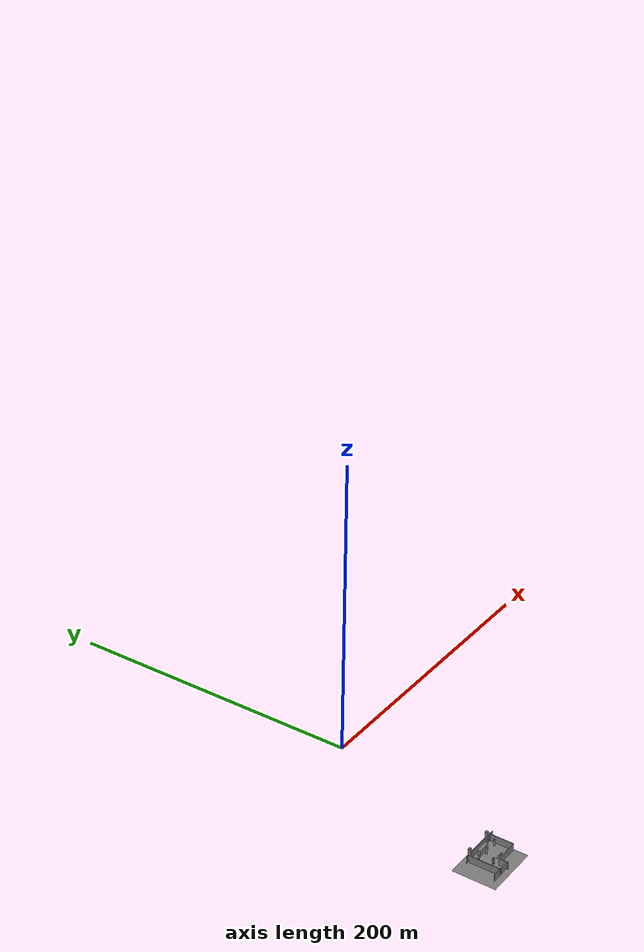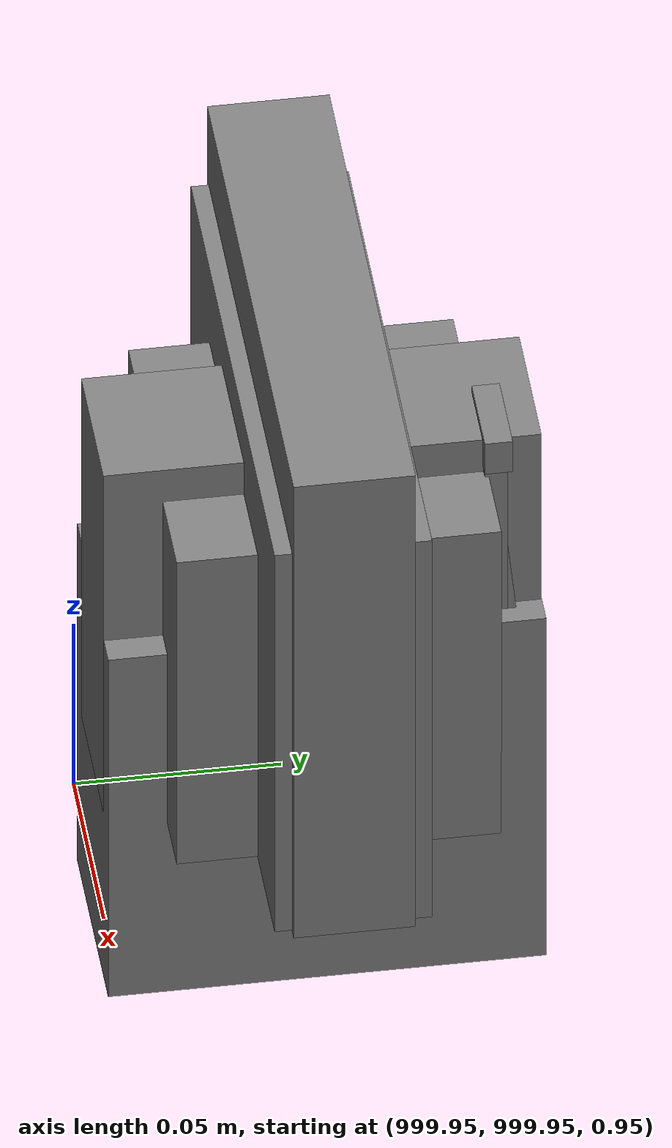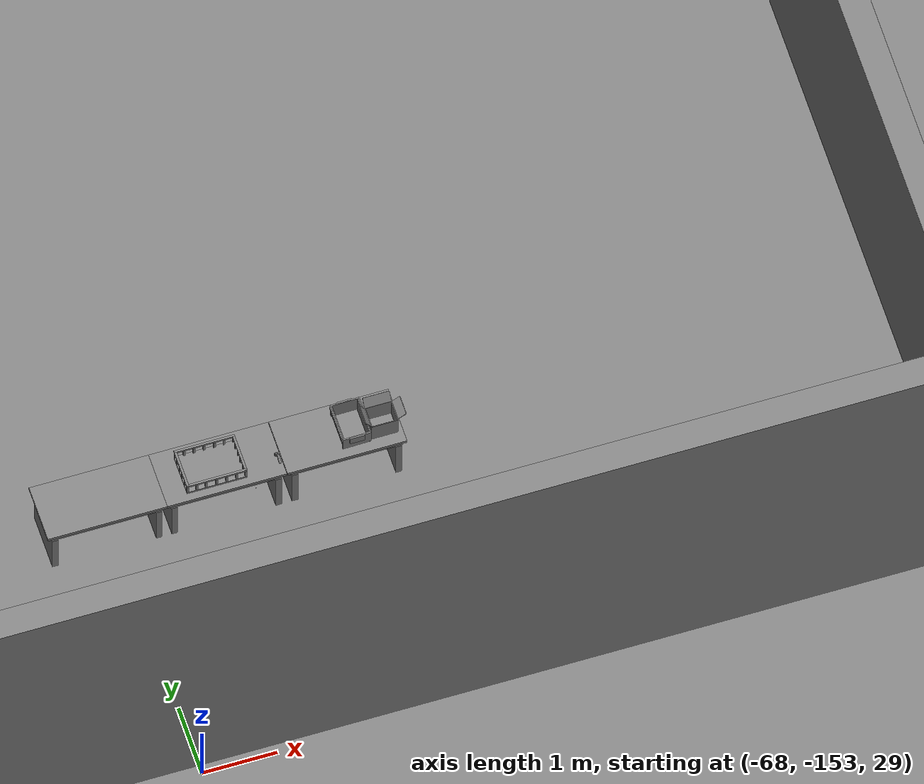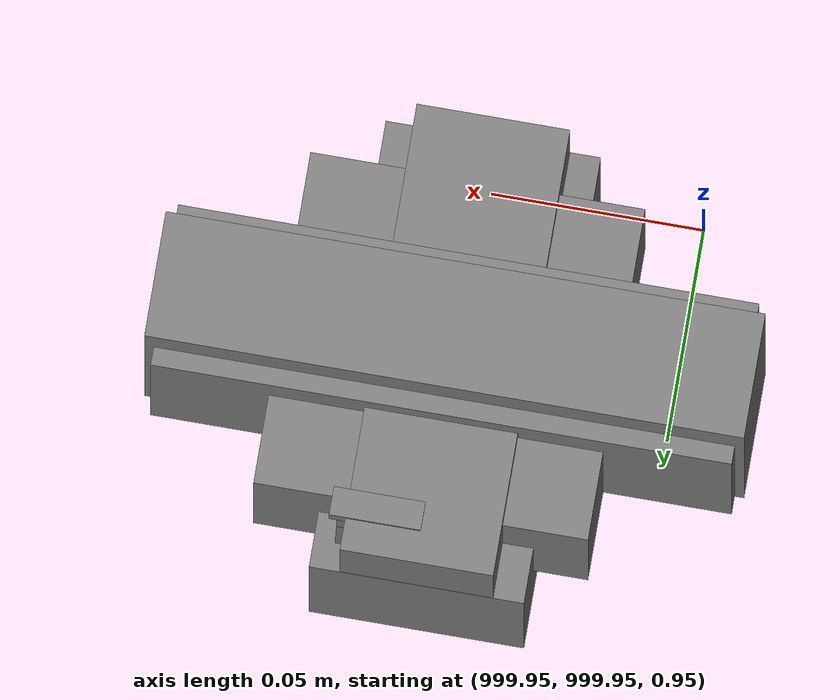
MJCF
<mujoco>
    <option gravity="0.000000000 0.000000000 -9.810000420" timestep="0.0049999999" integrator="implicitfast" density="1.225" viscosity="1.8000001e-05" noslip_iterations="10" iterations="100" sdf_iterations="50">
        <flag multiccd="disable"/>
    </option>
    <size memory="1000M"/>
    <compiler coordinate="local"/>
    <worldbody>
        <light cutoff="30" pos="0 1 1" dir="0 -1 -2"/>
        <light cutoff="30" pos="0 -1 1" dir="0 1 -2"/>
        <body pos="-66.210899353 -148.852081299 31.163555145" euler="-128.455886841 -67.570762634 -39.556552887" mocap="true" name="spotlight6_SpotLight"/>
        <body pos="1000.000000000 1000.000000000 1.000000000" euler="0.000000000 0.000000000 180.000000000" name="openloong_gripper_2f85_fix_base_usda_wifi_box">
            <geom contype="1" conaffinity="1" density="1000" type="box" material="" rgba="0.500000000 0.500000000 0.500000000 1.000000000" solimp="0.899999976 0.949999988 0.001000000" friction="1.000000000 0.005000000 0.000100000" solref="0.020000000 1.000000000" margin="0" condim="3" group="0" pos="0.000000000 0.000000000 0.058978677" quat="0.000000000 0.000000047 0.000000000 1.000000000" size="0.068499997 0.018999999 0.059000000" name="openloong_gripper_2f85_fix_base_usda_geom_AFD023B3_071E_4488_9BCF_8BE61D15B5A1"/>
            <freejoint name="openloong_gripper_2f85_fix_base_usda_wifi_box_joint"/>
            <site size="0.005000000 0.005000000 0.005000000" rgba="0.500000000 0.500000000 0.500000000 1.000000000" pos="0.000000000 0.000000000 0.000000000" quat="0.999961913 0.008726500 0.000000000 0.000000000" group="0" type="sphere" name="openloong_gripper_2f85_fix_base_usda_wifi_boxsite"/>
        </body>
        <body pos="1000.000000000 1000.000000000 1.000000000" euler="0.000000000 0.000000000 180.000000000" name="openloong_gripper_2f85_fix_base_usda_cpu_fan">
            <geom contype="1" conaffinity="1" density="1000" type="box" material="" rgba="0.500000000 0.500000000 0.500000000 1.000000000" solimp="0.899999976 0.949999988 0.001000000" friction="1.000000000 0.005000000 0.000100000" solref="0.020000000 1.000000000" margin="0" condim="3" group="0" pos="0.000000000 0.000000000 0.070034981" quat="0.000000000 0.000000000 0.000000000 1.000000000" size="0.070700005 0.014699999 0.070700005" name="openloong_gripper_2f85_fix_base_usda_geom_81DA2684_C821_4314_8A51_B85D80FEECA6"/>
            <freejoint name="openloong_gripper_2f85_fix_base_usda_cpu_fan_joint"/>
            <site size="0.005000000 0.005000000 0.005000000" rgba="0.500000000 0.500000000 0.500000000 1.000000000" pos="0.000000000 0.000000000 0.000000000" quat="0.999961913 0.008726535 0.000000000 0.000000000" group="0" type="sphere" name="openloong_gripper_2f85_fix_base_usda_cpu_fancsite"/>
        </body>
        <body pos="-66.207954407 -148.819885254 31.167974472" euler="-103.947891235 71.042991638 -68.889480591" mocap="true" name="spotlight3_SpotLight"/>
        <body pos="1000.000000000 1000.000000000 1.000000000" euler="0.000000000 0.000000000 180.000000000" name="openloong_gripper_2f85_fix_base_usda_battery_01">
            <geom contype="1" conaffinity="1" density="1000" type="box" material="" rgba="0.500000000 0.500000000 0.500000000 1.000000000" solimp="0.899999976 0.949999988 0.001000000" friction="1.000000000 0.005000000 0.000100000" solref="0.020000000 1.000000000" margin="0" condim="3" group="0" pos="-0.011123657 -0.041940309 0.101691343" quat="1.000000000 0.000000000 0.000000000 0.000000000" size="0.010800000 0.003375000 0.004725000" name="openloong_gripper_2f85_fix_base_usda_geom_988B5904_6276_40D2_89BF_E8576AFE4259"/>
            <geom contype="1" conaffinity="1" density="1000" type="box" material="" rgba="0.500000000 0.500000000 0.500000000 1.000000000" solimp="0.899999976 0.949999988 0.001000000" friction="1.000000000 0.005000000 0.000100000" solref="0.020000000 1.000000000" margin="0" condim="3" group="0" pos="-0.010876465 -0.044247437 0.047066893" quat="0.998702705 -0.050920475 0.000000000 0.000000000" size="0.009450001 0.002700000 0.024975000" name="openloong_gripper_2f85_fix_base_usda_geom_DFF44971_305E_4C42_962D_3AD3438FBC7E"/>
            <geom contype="1" conaffinity="1" density="1000" type="box" material="" rgba="0.500000000 0.500000000 0.500000000 1.000000000" solimp="0.899999976 0.949999988 0.001000000" friction="1.000000000 0.005000000 0.000100000" solref="0.020000000 1.000000000" margin="0" condim="3" group="0" pos="-0.001235962 -0.000659180 0.047381196" quat="1.000000000 0.000000000 0.000000000 0.000000000" size="0.039420001 0.039150000 0.047250003" name="openloong_gripper_2f85_fix_base_usda_geom_CA4DD9E9_C18A_4301_AE87_5F8244B652FE"/>
            <geom contype="1" conaffinity="1" density="1000" type="box" material="" rgba="0.500000000 0.500000000 0.500000000 1.000000000" solimp="0.899999976 0.949999988 0.001000000" friction="1.000000000 0.005000000 0.000100000" solref="0.020000000 1.000000000" margin="0" condim="3" group="0" pos="-0.010876465 -0.039138794 0.009851727" quat="1.000000000 0.000000000 0.000000000 0.000000000" size="0.009450001 0.010800000 0.013500000" name="openloong_gripper_2f85_fix_base_usda_geom_E8EA4684_E49A_401C_8CB1_3770E8934A6A"/>
            <geom contype="1" conaffinity="1" density="1000" type="box" material="" rgba="0.500000000 0.500000000 0.500000000 1.000000000" solimp="0.899999976 0.949999988 0.001000000" friction="1.000000000 0.005000000 0.000100000" solref="0.020000000 1.000000000" margin="0" condim="3" group="0" pos="-0.010876465 -0.041528322 0.071508206" quat="1.000000000 0.000000000 0.000000000 0.000000000" size="0.009450001 0.002700000 0.027000001" name="openloong_gripper_2f85_fix_base_usda_geom_B58529F5_AC5B_48A5_83EB_239344C2C50D"/>
            <freejoint name="openloong_gripper_2f85_fix_base_usda_battery_01_joint"/>
            <site size="0.005000000 0.005000000 0.005000000" rgba="0.500000000 0.500000000 0.500000000 1.000000000" pos="0.000000000 0.000000000 0.000000000" quat="0.999961913 0.008726500 0.000000000 0.000000000" group="0" type="sphere" name="openloong_gripper_2f85_fix_base_usda_battery_01site"/>
        </body>
        <body pos="1000.000000000 1000.000000000 1.000000000" euler="0.000011953 0.000005123 -179.999984741" name="openloong_gripper_2f85_fix_base_usda_intel_box">
            <geom contype="1" conaffinity="1" density="1000" type="box" material="" rgba="0.500000000 0.500000000 0.500000000 1.000000000" solimp="0.899999976 0.949999988 0.001000000" friction="1.000000000 0.005000000 0.000100000" solref="0.020000000 1.000000000" margin="0" condim="3" group="0" pos="0.000000000 -0.000067139 0.000082284" quat="0.707106709 0.000000225 0.000000253 0.707106650" size="0.052800003 0.025300000 0.052800003" name="openloong_gripper_2f85_fix_base_usda_geom_5C3ECC61_C1BE_44D7_9FC8_664C69BC99E6"/>
            <freejoint name="openloong_gripper_2f85_fix_base_usda_intel_box_joint"/>
            <site size="0.005000000 0.005000000 0.005000000" rgba="0.500000000 0.500000000 0.500000000 1.000000000" pos="0.000000000 0.000000000 0.000000000" quat="0.999961913 0.008726500 0.000000000 0.000000000" group="0" type="sphere" name="openloong_gripper_2f85_fix_base_usda_intel_boxsite"/>
        </body>
        <body pos="1000.000000000 999.999938965 1.000000000" euler="0.000000000 0.000000000 180.000000000" name="openloong_gripper_2f85_fix_base_usda_intelcore_i5">
            <geom contype="1" conaffinity="1" density="1000" type="box" material="" rgba="0.500000000 0.500000000 0.500000000 1.000000000" solimp="0.899999976 0.949999988 0.001000000" friction="1.000000000 0.005000000 0.000100000" solref="0.020000000 1.000000000" margin="0" condim="3" group="0" pos="0.000000000 0.000000000 0.051722717" quat="0.707106709 0.000000000 0.000000000 -0.707106769" size="0.052800000 0.018080002 0.052800000" name="openloong_gripper_2f85_fix_base_usda_geom_A477C694_439A_4E8F_B1C5_E99CBDD4C2AC"/>
            <freejoint name="openloong_gripper_2f85_fix_base_usda_intelcore_i5_joint"/>
            <site size="0.005000000 0.005000000 0.005000000" rgba="0.500000000 0.500000000 0.500000000 1.000000000" pos="0.000000000 0.000000000 0.000000000" quat="0.999961913 0.008726534 0.000000000 0.000000000" group="0" type="sphere" name="openloong_gripper_2f85_fix_base_usda_intelcore_i5site"/>
        </body>
        <body pos="-66.138671875 -148.883132935 31.166982651" euler="113.750541687 61.262313843 -159.488998413" mocap="true" name="spotlight4_SpotLight"/>
        <body pos="-64.866622925 -149.383972168 30.183746338" euler="89.999984741 89.999946594 0.000000000" name="openloong_gripper_2f85_fix_base_usda_bluebox_01">
            <geom contype="1" conaffinity="1" density="1000" type="box" material="" rgba="0.500000000 0.500000000 0.500000000 1.000000000" solimp="0.899999976 0.949999988 0.001000000" friction="1.000000000 0.005000000 0.000100000" solref="0.020000000 1.000000000" margin="0" condim="3" group="0" pos="0.276580811 0.187225342 0.000068665" quat="0.707106948 0.000077471 0.707106352 0.000077486" size="0.100000001 0.057999998 0.010000000" name="openloong_gripper_2f85_fix_base_usda_geom_A0135C7F_C1A2_41CE_8CEE_B90FBB4A6E52"/>
            <geom contype="1" conaffinity="1" density="1000" type="box" material="" rgba="0.500000000 0.500000000 0.500000000 1.000000000" solimp="0.899999976 0.949999988 0.001000000" friction="1.000000000 0.005000000 0.000100000" solref="0.020000000 1.000000000" margin="0" condim="3" group="0" pos="0.000000000 0.002883911 0.000000000" quat="0.999999881 0.000000000 0.000000000 0.000000000" size="0.254000008 0.003000000 0.172000006" name="openloong_gripper_2f85_fix_base_usda_geom_EC1FE949_3F25_4AB2_A716_696A5377F9FE"/>
            <geom contype="1" conaffinity="1" density="1000" type="box" material="" rgba="0.500000000 0.500000000 0.500000000 1.000000000" solimp="0.899999976 0.949999988 0.001000000" friction="1.000000000 0.005000000 0.000100000" solref="0.020000000 1.000000000" margin="0" condim="3" group="0" pos="0.000000000 0.124874115 0.173484802" quat="0.999796331 0.020176515 -0.000000015 0.000000030" size="0.259999990 0.119999997 0.007000000" name="openloong_gripper_2f85_fix_base_usda_geom_CD1F9046_D09B_482E_BAAB_E8CD606F0CC7"/>
            <geom contype="1" conaffinity="1" density="1000" type="box" material="" rgba="0.500000000 0.500000000 0.500000000 1.000000000" solimp="0.899999976 0.949999988 0.001000000" friction="1.000000000 0.005000000 0.000100000" solref="0.020000000 1.000000000" margin="0" condim="3" group="0" pos="0.000000000 0.124874115 -0.173469543" quat="0.999796331 -0.020176545 -0.000000015 0.000000000" size="0.259999990 0.119999997 0.007000000" name="openloong_gripper_2f85_fix_base_usda_geom_ED040640_678F_4E37_B1E8_D695447C9282"/>
            <geom contype="1" conaffinity="1" density="1000" type="box" material="" rgba="0.500000000 0.500000000 0.500000000 1.000000000" solimp="0.899999976 0.949999988 0.001000000" friction="1.000000000 0.005000000 0.000100000" solref="0.020000000 1.000000000" margin="0" condim="3" group="0" pos="0.000000000 0.214008331 0.188980103" quat="0.999912977 0.013176724 0.000000015 0.000000000" size="0.259999990 0.029999999 0.012500000" name="openloong_gripper_2f85_fix_base_usda_geom_E0DF048F_6577_4428_8E40_82407DB6DE28"/>
            <geom contype="1" conaffinity="1" density="1000" type="box" material="" rgba="0.500000000 0.500000000 0.500000000 1.000000000" solimp="0.899999976 0.949999988 0.001000000" friction="1.000000000 0.005000000 0.000100000" solref="0.020000000 1.000000000" margin="0" condim="3" group="0" pos="-0.258361816 0.125289917 0.001876831" quat="0.702796936 -0.020792112 0.710783124 0.020769298" size="0.189999998 0.119999997 0.009000000" name="openloong_gripper_2f85_fix_base_usda_geom_789B439F_F158_4102_BB10_83E024174D20"/>
            <geom contype="1" conaffinity="1" density="1000" type="box" material="" rgba="0.500000000 0.500000000 0.500000000 1.000000000" solimp="0.899999976 0.949999988 0.001000000" friction="1.000000000 0.005000000 0.000100000" solref="0.020000000 1.000000000" margin="0" condim="3" group="0" pos="0.000000000 0.214008331 -0.188980103" quat="0.999912977 -0.013176769 0.000000030 0.000000015" size="0.259999990 0.029999999 0.012500000" name="openloong_gripper_2f85_fix_base_usda_geom_E50C6DD0_D8BD_4E88_838E_98BE8C1C347E"/>
            <geom contype="1" conaffinity="1" density="1000" type="box" material="" rgba="0.500000000 0.500000000 0.500000000 1.000000000" solimp="0.899999976 0.949999988 0.001000000" friction="1.000000000 0.005000000 0.000100000" solref="0.020000000 1.000000000" margin="0" condim="3" group="0" pos="-0.276611328 0.187225342 0.000068665" quat="0.707106650 0.000077441 0.707106709 0.000077456" size="0.100000001 0.057999998 0.010000000" name="openloong_gripper_2f85_fix_base_usda_geom_55534C86_0AC5_4CB5_9C9D_9F58F4B13B0C"/>
            <geom contype="1" conaffinity="1" density="1000" type="box" material="" rgba="0.500000000 0.500000000 0.500000000 1.000000000" solimp="0.899999976 0.949999988 0.001000000" friction="1.000000000 0.005000000 0.000100000" solref="0.020000000 1.000000000" margin="0" condim="3" group="0" pos="0.258331299 0.125289917 0.001876831" quat="0.702851415 0.018856421 0.710823774 -0.019329369" size="0.189999998 0.119999997 0.009000000" name="openloong_gripper_2f85_fix_base_usda_geom_C520BB4E_8428_488D_9BCF_7689483ECBA1"/>
            <freejoint name="openloong_gripper_2f85_fix_base_usda_bluebox_01_joint"/>
            <site size="0.005000000 0.005000000 0.005000000" rgba="0.500000000 0.500000000 0.500000000 1.000000000" pos="0.000000000 0.000000000 0.000000000" quat="0.999961913 0.008726534 0.000000000 0.000000000" group="0" type="sphere" name="openloong_gripper_2f85_fix_base_usda_bluebox_01site"/>
        </body>
        <body pos="-64.496299744 -149.491867065 30.235729218" euler="0.000000000 0.000000000 89.999946594" name="openloong_gripper_2f85_fix_base_usda_cardboardbox_01">
            <geom contype="1" conaffinity="1" density="1000" type="box" material="" rgba="0.500000000 0.500000000 0.500000000 1.000000000" solimp="0.899999976 0.949999988 0.001000000" friction="1.000000000 0.005000000 0.000100000" solref="0.020000000 1.000000000" margin="0" condim="3" group="0" pos="-0.003166199 -0.004086494 0.005052090" quat="1.000000000 0.000000000 0.000000000 0.000000000" size="0.142499998 0.177500010 0.005000000" name="openloong_gripper_2f85_fix_base_usda_geom_BC42881A_FE25_4B4F_8AF3_F4F08F735245"/>
            <geom contype="1" conaffinity="1" density="1000" type="box" material="" rgba="0.500000000 0.500000000 0.500000000 1.000000000" solimp="0.899999976 0.949999988 0.001000000" friction="1.000000000 0.005000000 0.000100000" solref="0.020000000 1.000000000" margin="0" condim="3" group="0" pos="-0.003166199 0.170316696 0.150570869" quat="1.000000000 0.000000000 0.000000000 0.000000000" size="0.142499998 0.005000000 0.149999991" name="openloong_gripper_2f85_fix_base_usda_geom_43DEC29E_9406_4B07_975B_B98A2571135A"/>
            <geom contype="1" conaffinity="1" density="1000" type="box" material="" rgba="0.500000000 0.500000000 0.500000000 1.000000000" solimp="0.899999976 0.949999988 0.001000000" friction="1.000000000 0.005000000 0.000100000" solref="0.020000000 1.000000000" margin="0" condim="3" group="0" pos="-0.147399902 -0.005307198 0.150570869" quat="1.000000000 0.000000000 0.000000000 0.000000000" size="0.005000000 0.177500010 0.149999991" name="openloong_gripper_2f85_fix_base_usda_geom_A3B87101_B50A_4F7C_83D5_1F550AE1410A"/>
            <geom contype="1" conaffinity="1" density="1000" type="box" material="" rgba="0.500000000 0.500000000 0.500000000 1.000000000" solimp="0.899999976 0.949999988 0.001000000" friction="1.000000000 0.005000000 0.000100000" solref="0.020000000 1.000000000" margin="0" condim="3" group="0" pos="0.140275955 -0.005307198 0.150570869" quat="1.000000000 0.000000000 0.000000000 0.000000000" size="0.005000000 0.177500010 0.149999991" name="openloong_gripper_2f85_fix_base_usda_geom_C80FFD47_277F_450B_A291_35EBC7D342C3"/>
            <geom contype="1" conaffinity="1" density="1000" type="box" material="" rgba="0.500000000 0.500000000 0.500000000 1.000000000" solimp="0.899999976 0.949999988 0.001000000" friction="1.000000000 0.005000000 0.000100000" solref="0.020000000 1.000000000" margin="0" condim="3" group="0" pos="-0.003166199 -0.181550980 0.150570869" quat="1.000000000 0.000000000 0.000000000 0.000000000" size="0.142499998 0.005000000 0.149999991" name="openloong_gripper_2f85_fix_base_usda_geom_DD65A8AE_1674_4BA8_A544_4407905B5C46"/>
            <freejoint name="openloong_gripper_2f85_fix_base_usda_cardboardbox_01_joint"/>
            <site size="0.005000000 0.005000000 0.005000000" rgba="0.500000000 0.500000000 0.500000000 1.000000000" pos="0.000000000 0.000000000 0.000000000" quat="0.999961913 0.008726535 0.000000000 0.000000000" group="0" type="sphere" name="openloong_gripper_2f85_fix_base_usda_site_9B0B7F09_E853_4DA1_8D05_5E0E88303022"/>
            <body pos="0.139160156 -0.004048347 0.301930904" euler="-179.999954224 49.383502960 179.999954224" name="openloong_gripper_2f85_fix_base_usda_A1_006">
                <geom contype="1" conaffinity="1" density="1000" type="box" material="" rgba="0.500000000 0.500000000 0.500000000 1.000000000" solimp="0.899999976 0.949999988 0.001000000" friction="1.000000000 0.005000000 0.000100000" solref="0.020000000 1.000000000" margin="0" condim="3" group="0" pos="-0.071587563 0.000009537 0.001745224" quat="0.999999881 0.000000000 0.000000000 0.000000000" size="0.071249999 0.179999992 0.002500000" name="openloong_gripper_2f85_fix_base_usda_geom_4EE4477D_31A2_470A_97FE_F66B97A7671F"/>
                <joint armature="0" stiffness="0.07" damping="0.0099999998" axis="0.000000 1.000000 0.000000" type="hinge" name="openloong_gripper_2f85_fix_base_usda_A1_006"/>
            </body>
            <body pos="-0.145902634 -0.004086494 0.301938057" euler="-180.000000000 -60.000011444 -180.000000000" name="openloong_gripper_2f85_fix_base_usda_A2_006">
                <geom contype="1" conaffinity="1" density="1000" type="box" material="" rgba="0.500000000 0.500000000 0.500000000 1.000000000" solimp="0.899999976 0.949999988 0.001000000" friction="1.000000000 0.005000000 0.000100000" solref="0.020000000 1.000000000" margin="0" condim="3" group="0" pos="0.071268082 0.000009537 0.002717972" quat="0.000002921 0.000000000 -0.000000030 0.999999881" size="0.071249999 0.179999992 0.002500000" name="openloong_gripper_2f85_fix_base_usda_geom_4812C3AA_4D08_473B_8D44_6AA0F70797D0"/>
                <joint armature="0" stiffness="0.07" damping="0.0099999998" axis="0.000000 1.000000 0.000000" type="hinge" name="openloong_gripper_2f85_fix_base_usda_A2_006"/>
            </body>
            <body pos="-0.003385544 0.175991058 0.301930904" euler="-125.858116150 -0.000004561 0.000002331" name="openloong_gripper_2f85_fix_base_usda_B2_006">
                <geom contype="1" conaffinity="1" density="1000" type="box" material="" rgba="0.500000000 0.500000000 0.500000000 1.000000000" solimp="0.899999976 0.949999988 0.001000000" friction="1.000000000 0.005000000 0.000100000" solref="0.020000000 1.000000000" margin="0" condim="3" group="0" pos="0.000009537 -0.070939064 -0.002470016" quat="0.999614120 0.027776197 -0.000000015 0.000000030" size="0.137500003 0.064999998 0.005000000" name="openloong_gripper_2f85_fix_base_usda_geom_0025DFFB_C635_4290_9DD4_B351D48561F3"/>
                <joint armature="0" stiffness="0.07" damping="0.0099999998" axis="1.000000 0.000000 0.000000" type="hinge" name="openloong_gripper_2f85_fix_base_usda_B2_006"/>
            </body>
            <body pos="-0.003385544 -0.184140205 0.301938057" euler="147.805557251 0.000000000 0.000000000" name="openloong_gripper_2f85_fix_base_usda_B1_006">
                <geom contype="1" conaffinity="1" density="1000" type="box" material="" rgba="0.500000000 0.500000000 0.500000000 1.000000000" solimp="0.899999976 0.949999988 0.001000000" friction="1.000000000 0.005000000 0.000100000" solref="0.020000000 1.000000000" margin="0" condim="3" group="0" pos="-0.000028610 0.070202351 -0.002703667" quat="0.999614179 -0.027776167 0.000000000 0.000000000" size="0.137500003 0.064999998 0.005000000" name="openloong_gripper_2f85_fix_base_usda_geom_BE214892_74FC_4FBB_95B8_7C4AF40ACF5A"/>
                <joint armature="0" stiffness="0.07" damping="0.0099999998" axis="1.000000 0.000000 0.000000" type="hinge" name="openloong_gripper_2f85_fix_base_usda_B1_006"/>
            </body>
        </body>
        <body pos="-65.882858276 -149.481979370 30.229999542" euler="-64.487716675 0.000000000 0.000000000" name="openloong_gripper_2f85_fix_base_usda_Barcode">
            <geom contype="1" conaffinity="1" density="1000" type="box" material="" rgba="0.500000000 0.500000000 0.500000000 1.000000000" solimp="0.899999976 0.949999988 0.001000000" friction="1.000000000 0.005000000 0.000100000" solref="0.020000000 1.000000000" margin="0" condim="3" group="0" pos="0.000000000 0.013038635 0.001419067" quat="0.000000000 0.000000000 0.000000000 1.000000119" size="0.034000002 0.010000000 0.017999999" name="openloong_gripper_2f85_fix_base_usda_geom_A4EC8BDA_1802_4155_A4FB_5023DE1BEF52"/>
            <geom contype="1" conaffinity="1" density="1000" type="box" material="" rgba="0.500000000 0.500000000 0.500000000 1.000000000" solimp="0.899999976 0.949999988 0.001000000" friction="1.000000000 0.005000000 0.000100000" solref="0.020000000 1.000000000" margin="0" condim="3" group="0" pos="0.000000000 -0.035301208 -0.007095337" quat="0.000000000 0.000000000 -0.043619365 0.999048233" size="0.028999999 0.010000000 0.020000000" name="openloong_gripper_2f85_fix_base_usda_geom_D4030C18_CEB3_4CAC_8BFE_A56F6D93F6C8"/>
            <geom contype="1" conaffinity="1" density="1000" type="box" material="" rgba="0.500000000 0.500000000 0.500000000 1.000000000" solimp="0.899999976 0.949999988 0.001000000" friction="1.000000000 0.005000000 0.000100000" solref="0.020000000 1.000000000" margin="0" condim="3" group="0" pos="0.000000000 -0.043411255 -0.011749268" quat="0.922262907 0.386563420 0.000000000 0.000000000" size="0.026000001 0.010000000 0.020000000" name="openloong_gripper_2f85_fix_base_usda_geom_C3C05EE1_7140_4FD1_8DBE_7D0447AF9160"/>
            <geom contype="1" conaffinity="1" density="1000" type="box" material="" rgba="0.500000000 0.500000000 0.500000000 1.000000000" solimp="0.899999976 0.949999988 0.001000000" friction="1.000000000 0.005000000 0.000100000" solref="0.020000000 1.000000000" margin="0" condim="3" group="0" pos="0.000000000 -0.016967773 -0.031860352" quat="0.000000000 0.000000000 0.000000000 1.000000119" size="0.008000000 0.010000000 0.013000000" name="openloong_gripper_2f85_fix_base_usda_geom_48111122_E3EE_470D_A19D_3521BA33A3E1"/>
            <geom contype="1" conaffinity="1" density="1000" type="box" material="" rgba="0.500000000 0.500000000 0.500000000 1.000000000" solimp="0.899999976 0.949999988 0.001000000" friction="1.000000000 0.005000000 0.000100000" solref="0.020000000 1.000000000" margin="0" condim="3" group="0" pos="0.000000000 -0.001869202 0.000312805" quat="0.953716993 0.300705761 0.000000000 0.000000000" size="0.032000002 0.010000000 0.018999999" name="openloong_gripper_2f85_fix_base_usda_geom_6EE83586_A906_44AE_97BD_7FEA6BA80C77"/>
            <geom contype="1" conaffinity="1" density="1000" type="box" material="" rgba="0.500000000 0.500000000 0.500000000 1.000000000" solimp="0.899999976 0.949999988 0.001000000" friction="1.000000000 0.005000000 0.000100000" solref="0.020000000 1.000000000" margin="0" condim="3" group="0" pos="0.000000000 -0.019531250 -0.003173828" quat="0.953716993 0.300705761 0.000000000 0.000000000" size="0.030999999 0.010000000 0.020000000" name="openloong_gripper_2f85_fix_base_usda_geom_5B3323BF_A649_4EDF_8CBD_061129D14BD2"/>
            <geom contype="1" conaffinity="1" density="1000" type="box" material="" rgba="0.500000000 0.500000000 0.500000000 1.000000000" solimp="0.899999976 0.949999988 0.001000000" friction="1.000000000 0.005000000 0.000100000" solref="0.020000000 1.000000000" margin="0" condim="3" group="0" pos="0.000000000 -0.035301208 -0.007095337" quat="0.953716993 0.300705761 0.000000000 0.000000000" size="0.028999999 0.010000000 0.020000000" name="openloong_gripper_2f85_fix_base_usda_geom_853DF064_9EDD_4FA6_86F3_9D23C94895EB"/>
            <geom contype="1" conaffinity="1" density="1000" type="box" material="" rgba="0.500000000 0.500000000 0.500000000 1.000000000" solimp="0.899999976 0.949999988 0.001000000" friction="1.000000000 0.005000000 0.000100000" solref="0.020000000 1.000000000" margin="0" condim="3" group="0" pos="0.000000000 -0.042617798 -0.071121216" quat="0.000000000 0.000000000 0.000000000 1.000000119" size="0.013000000 0.021000000 0.059999999" name="openloong_gripper_2f85_fix_base_usda_geom_49CB5B89_969C_4CF3_93FA_1AD66D005F3A"/>
            <freejoint name="openloong_gripper_2f85_fix_base_usda_Barcode_joint"/>
            <site size="0.005000000 0.005000000 0.005000000" rgba="0.500000000 0.500000000 0.500000000 1.000000000" pos="0.000000000 0.000000000 0.000000000" quat="1.000000000 0.000000000 0.000000000 0.000000000" group="0" type="sphere" name="openloong_gripper_2f85_fix_base_usda_Barcode_site"/>
        </body>
        <body pos="-66.745018005 -149.392349243 30.184000015" euler="0.000000000 0.000000000 89.999946594" name="[22333427545318]_Basket_01">
            <geom contype="1" conaffinity="1" density="1000" type="box" material="" rgba="0.500000000 0.500000000 0.500000000 1.000000000" solimp="0.899999976 0.949999988 0.001000000" friction="1.000000000 0.005000000 0.000100000" solref="0.020000000 1.000000000" margin="0" condim="3" group="0" pos="-0.052425385 0.389207840 0.089787483" quat="0.707107008 0.000000000 0.000000000 0.707106411" size="0.014249999 0.014249999 0.059999999" name="[22333427545318]_geom_66284A04_E864_4621_8B0B_61FC12DDCBCB"/>
            <geom contype="1" conaffinity="1" density="1000" type="box" material="" rgba="0.500000000 0.500000000 0.500000000 1.000000000" solimp="0.899999976 0.949999988 0.001000000" friction="1.000000000 0.005000000 0.000100000" solref="0.020000000 1.000000000" margin="0" condim="3" group="0" pos="0.264015198 -0.133043289 0.089787483" quat="0.707107008 0.000000000 0.000000000 0.707106411" size="0.014249999 0.014249999 0.059999999" name="[22333427545318]_geom_D736D9D5_9F74_4752_B9E4_E88EA331B5F5"/>
            <geom contype="1" conaffinity="1" density="1000" type="box" material="" rgba="0.500000000 0.500000000 0.500000000 1.000000000" solimp="0.899999976 0.949999988 0.001000000" friction="1.000000000 0.005000000 0.000100000" solref="0.020000000 1.000000000" margin="0" condim="3" group="0" pos="-0.264015198 -0.265548706 0.089793205" quat="0.707107008 0.000000000 0.000000000 0.707106411" size="0.014249999 0.014249999 0.059999999" name="[22333427545318]_geom_93E1D5C6_E074_4C03_9F43_6199AD481338"/>
            <geom contype="1" conaffinity="1" density="1000" type="box" material="" rgba="0.500000000 0.500000000 0.500000000 1.000000000" solimp="0.899999976 0.949999988 0.001000000" friction="1.000000000 0.005000000 0.000100000" solref="0.020000000 1.000000000" margin="0" condim="3" group="0" pos="-0.160263062 -0.389322281 0.089793205" quat="0.707107008 0.000000000 0.000000000 0.707106411" size="0.014249999 0.014249999 0.059999999" name="[22333427545318]_geom_859C2203_3178_4C37_97EA_D6313344E262"/>
            <geom contype="1" conaffinity="1" density="1000" type="box" material="" rgba="0.500000000 0.500000000 0.500000000 1.000000000" solimp="0.899999976 0.949999988 0.001000000" friction="1.000000000 0.005000000 0.000100000" solref="0.020000000 1.000000000" margin="0" condim="3" group="0" pos="0.162265778 -0.389322281 0.089787483" quat="0.707107008 0.000000000 0.000000000 0.707106411" size="0.014249999 0.014249999 0.059999999" name="[22333427545318]_geom_AC5B2A95_BA5A_4246_BFED_96641F863796"/>
            <geom contype="1" conaffinity="1" density="1000" type="box" material="" rgba="0.500000000 0.500000000 0.500000000 1.000000000" solimp="0.899999976 0.949999988 0.001000000" friction="1.000000000 0.005000000 0.000100000" solref="0.020000000 1.000000000" margin="0" condim="3" group="0" pos="0.264015198 0.389207840 0.089787483" quat="0.707107008 0.000000000 0.000000000 0.707106411" size="0.014249999 0.014249999 0.059999999" name="[22333427545318]_geom_3C058F7F_69EC_4F6A_A1A3_D5572591C48E"/>
            <geom contype="1" conaffinity="1" density="1000" type="box" material="" rgba="0.500000000 0.500000000 0.500000000 1.000000000" solimp="0.899999976 0.949999988 0.001000000" friction="1.000000000 0.005000000 0.000100000" solref="0.020000000 1.000000000" margin="0" condim="3" group="0" pos="-0.264015198 -0.133043289 0.089793205" quat="0.707107008 0.000000000 0.000000000 0.707106411" size="0.014249999 0.014249999 0.059999999" name="[22333427545318]_geom_21EB526D_4ACB_41B1_93DD_18195B76943F"/>
            <geom contype="1" conaffinity="1" density="1000" type="box" material="" rgba="0.500000000 0.500000000 0.500000000 1.000000000" solimp="0.899999976 0.949999988 0.001000000" friction="1.000000000 0.005000000 0.000100000" solref="0.020000000 1.000000000" margin="0" condim="3" group="0" pos="-0.264026642 0.269256592 0.089793205" quat="0.707107008 0.000000000 0.000000000 0.707106411" size="0.014249999 0.014249999 0.059999999" name="[22333427545318]_geom_850EDC76_4616_4761_888C_999DAC3D2FEF"/>
            <geom contype="1" conaffinity="1" density="1000" type="box" material="" rgba="0.500000000 0.500000000 0.500000000 1.000000000" solimp="0.899999976 0.949999988 0.001000000" friction="1.000000000 0.005000000 0.000100000" solref="0.020000000 1.000000000" margin="0" condim="3" group="0" pos="0.054462433 0.389207840 0.089787483" quat="0.707107008 0.000000000 0.000000000 0.707106411" size="0.014249999 0.014249999 0.059999999" name="[22333427545318]_geom_0337AEAB_3EFA_49A3_A143_7E9E51D294C9"/>
            <geom contype="1" conaffinity="1" density="1000" type="box" material="" rgba="0.500000000 0.500000000 0.500000000 1.000000000" solimp="0.899999976 0.949999988 0.001000000" friction="1.000000000 0.005000000 0.000100000" solref="0.020000000 1.000000000" margin="0" condim="3" group="0" pos="0.054462433 -0.389322281 0.089787483" quat="0.707107008 0.000000000 0.000000000 0.707106411" size="0.014249999 0.014249999 0.059999999" name="[22333427545318]_geom_9983E4BF_7598_4F9E_8E20_50433A444B05"/>
            <geom contype="1" conaffinity="1" density="1000" type="box" material="" rgba="0.500000000 0.500000000 0.500000000 1.000000000" solimp="0.899999976 0.949999988 0.001000000" friction="1.000000000 0.005000000 0.000100000" solref="0.020000000 1.000000000" margin="0" condim="3" group="0" pos="0.264015198 0.269256592 0.089793205" quat="0.707107008 0.000000000 0.000000000 0.707106411" size="0.014249999 0.014249999 0.059999999" name="[22333427545318]_geom_BB680053_1107_4DAC_ACD6_53F06DCD94AF"/>
            <geom contype="1" conaffinity="1" density="1000" type="box" material="" rgba="0.500000000 0.500000000 0.500000000 1.000000000" solimp="0.899999976 0.949999988 0.001000000" friction="1.000000000 0.005000000 0.000100000" solref="0.020000000 1.000000000" margin="0" condim="3" group="0" pos="0.264015198 -0.389322281 0.089787483" quat="0.707107008 0.000000000 0.000000000 0.707106411" size="0.014249999 0.014249999 0.059999999" name="[22333427545318]_geom_D3FB253D_2687_45B4_AA3B_7BA0C84972DA"/>
            <geom contype="1" conaffinity="1" density="1000" type="box" material="" rgba="0.500000000 0.500000000 0.500000000 1.000000000" solimp="0.899999976 0.949999988 0.001000000" friction="1.000000000 0.005000000 0.000100000" solref="0.020000000 1.000000000" margin="0" condim="3" group="0" pos="0.000000000 0.000000000 0.015998840" quat="0.707107008 0.000000000 0.000000000 0.707106411" size="0.403499991 0.279000014 0.015750000" name="[22333427545318]_geom_225C07FD_0CC3_4D4E_84CA_0666C19C8B4D"/>
            <geom contype="1" conaffinity="1" density="1000" type="box" material="" rgba="0.500000000 0.500000000 0.500000000 1.000000000" solimp="0.899999976 0.949999988 0.001000000" friction="1.000000000 0.005000000 0.000100000" solref="0.020000000 1.000000000" margin="0" condim="3" group="0" pos="0.000000000 -0.389476776 0.163619041" quat="0.707107008 0.000000000 0.000000000 0.707106411" size="0.015000000 0.277500004 0.015750000" name="[22333427545318]_geom_52713C1B_D3A4_491F_B98F_188BCAFB427C"/>
            <geom contype="1" conaffinity="1" density="1000" type="box" material="" rgba="0.500000000 0.500000000 0.500000000 1.000000000" solimp="0.899999976 0.949999988 0.001000000" friction="1.000000000 0.005000000 0.000100000" solref="0.020000000 1.000000000" margin="0" condim="3" group="0" pos="0.162265778 0.389207840 0.089787483" quat="0.707107008 0.000000000 0.000000000 0.707106411" size="0.014249999 0.014249999 0.059999999" name="[22333427545318]_geom_272F22F3_5371_46C3_9AEC_21CA638FA13E"/>
            <geom contype="1" conaffinity="1" density="1000" type="box" material="" rgba="0.500000000 0.500000000 0.500000000 1.000000000" solimp="0.899999976 0.949999988 0.001000000" friction="1.000000000 0.005000000 0.000100000" solref="0.020000000 1.000000000" margin="0" condim="3" group="0" pos="0.000000000 0.389471054 0.163619041" quat="0.707107008 0.000000000 0.000000000 0.707106411" size="0.015000000 0.277500004 0.015750000" name="[22333427545318]_geom_44D8EFD9_C677_465C_AAE2_C613DAD7D810"/>
            <geom contype="1" conaffinity="1" density="1000" type="box" material="" rgba="0.500000000 0.500000000 0.500000000 1.000000000" solimp="0.899999976 0.949999988 0.001000000" friction="1.000000000 0.005000000 0.000100000" solref="0.020000000 1.000000000" margin="0" condim="3" group="0" pos="-0.263511658 0.000000000 0.163619041" quat="0.707107008 0.000000000 0.000000000 0.707106411" size="0.403499991 0.015000000 0.015750000" name="[22333427545318]_geom_FF1C8E39_AC72_4381_B369_236CF9A3E094"/>
            <geom contype="1" conaffinity="1" density="1000" type="box" material="" rgba="0.500000000 0.500000000 0.500000000 1.000000000" solimp="0.899999976 0.949999988 0.001000000" friction="1.000000000 0.005000000 0.000100000" solref="0.020000000 1.000000000" margin="0" condim="3" group="0" pos="-0.264015198 0.141334534 0.089793205" quat="0.707107008 0.000000000 0.000000000 0.707106411" size="0.014249999 0.014249999 0.059999999" name="[22333427545318]_geom_B1813E76_14E5_4D13_971F_690FCA30DF93"/>
            <geom contype="1" conaffinity="1" density="1000" type="box" material="" rgba="0.500000000 0.500000000 0.500000000 1.000000000" solimp="0.899999976 0.949999988 0.001000000" friction="1.000000000 0.005000000 0.000100000" solref="0.020000000 1.000000000" margin="0" condim="3" group="0" pos="0.264015198 -0.265548706 0.089787483" quat="0.707107008 0.000000000 0.000000000 0.707106411" size="0.014249999 0.014249999 0.059999999" name="[22333427545318]_geom_D0055FCB_8FC7_41B4_B326_D7B1E762B45C"/>
            <geom contype="1" conaffinity="1" density="1000" type="box" material="" rgba="0.500000000 0.500000000 0.500000000 1.000000000" solimp="0.899999976 0.949999988 0.001000000" friction="1.000000000 0.005000000 0.000100000" solref="0.020000000 1.000000000" margin="0" condim="3" group="0" pos="-0.160263062 0.389207840 0.089787483" quat="0.707107008 0.000000000 0.000000000 0.707106411" size="0.014249999 0.014249999 0.059999999" name="[22333427545318]_geom_B8B36EB6_1458_4407_ACC8_EF3D025A35D4"/>
            <geom contype="1" conaffinity="1" density="1000" type="box" material="" rgba="0.500000000 0.500000000 0.500000000 1.000000000" solimp="0.899999976 0.949999988 0.001000000" friction="1.000000000 0.005000000 0.000100000" solref="0.020000000 1.000000000" margin="0" condim="3" group="0" pos="-0.052425385 -0.389322281 0.089787483" quat="0.707107008 0.000000000 0.000000000 0.707106411" size="0.014249999 0.014249999 0.059999999" name="[22333427545318]_geom_0D40F3F0_C91E_40F7_8079_465756DEE980"/>
            <geom contype="1" conaffinity="1" density="1000" type="box" material="" rgba="0.500000000 0.500000000 0.500000000 1.000000000" solimp="0.899999976 0.949999988 0.001000000" friction="1.000000000 0.005000000 0.000100000" solref="0.020000000 1.000000000" margin="0" condim="3" group="0" pos="-0.264026642 -0.389322281 0.089793205" quat="0.707107008 0.000000000 0.000000000 0.707106411" size="0.014249999 0.014249999 0.059999999" name="[22333427545318]_geom_B48D8A97_5A0C_4B26_934B_197991CE462E"/>
            <geom contype="1" conaffinity="1" density="1000" type="box" material="" rgba="0.500000000 0.500000000 0.500000000 1.000000000" solimp="0.899999976 0.949999988 0.001000000" friction="1.000000000 0.005000000 0.000100000" solref="0.020000000 1.000000000" margin="0" condim="3" group="0" pos="0.264015198 0.141334534 0.089787483" quat="0.707107008 0.000000000 0.000000000 0.707106411" size="0.014249999 0.014249999 0.059999999" name="[22333427545318]_geom_A17F63DA_1803_4896_A800_09D1D9CABB1C"/>
            <geom contype="1" conaffinity="1" density="1000" type="box" material="" rgba="0.500000000 0.500000000 0.500000000 1.000000000" solimp="0.899999976 0.949999988 0.001000000" friction="1.000000000 0.005000000 0.000100000" solref="0.020000000 1.000000000" margin="0" condim="3" group="0" pos="-0.264015198 0.389207840 0.089793205" quat="0.707107008 0.000000000 0.000000000 0.707106411" size="0.014249999 0.014249999 0.059999999" name="[22333427545318]_geom_6A6563D9_5EFB_4E8E_8AA5_74A36731A910"/>
            <geom contype="1" conaffinity="1" density="1000" type="box" material="" rgba="0.500000000 0.500000000 0.500000000 1.000000000" solimp="0.899999976 0.949999988 0.001000000" friction="1.000000000 0.005000000 0.000100000" solref="0.020000000 1.000000000" margin="0" condim="3" group="0" pos="0.264015198 0.004480362 0.089787483" quat="0.707107008 0.000000000 0.000000000 0.707106411" size="0.014249999 0.014249999 0.059999999" name="[22333427545318]_geom_4313F881_9DF0_43C1_87DD_743B5C9B4219"/>
            <geom contype="1" conaffinity="1" density="1000" type="box" material="" rgba="0.500000000 0.500000000 0.500000000 1.000000000" solimp="0.899999976 0.949999988 0.001000000" friction="1.000000000 0.005000000 0.000100000" solref="0.020000000 1.000000000" margin="0" condim="3" group="0" pos="0.263694763 -0.000011444 0.163619041" quat="0.707107008 0.000000000 0.000000000 0.707106411" size="0.403499991 0.015000000 0.015750000" name="[22333427545318]_geom_DB7C2888_8D84_4A6A_8A81_829C37F2B49A"/>
            <geom contype="1" conaffinity="1" density="1000" type="box" material="" rgba="0.500000000 0.500000000 0.500000000 1.000000000" solimp="0.899999976 0.949999988 0.001000000" friction="1.000000000 0.005000000 0.000100000" solref="0.020000000 1.000000000" margin="0" condim="3" group="0" pos="-0.264015198 0.004480362 0.089793205" quat="0.707107008 0.000000000 0.000000000 0.707106411" size="0.014249999 0.014249999 0.059999999" name="[22333427545318]_geom_B5EF8705_89C6_4198_AB9A_B356346FEF1F"/>
            <freejoint name="[22333427545318]_joint_4AD83972_43D0_4EBD_9089_DC0E94A86E9C"/>
        </body>
        <body pos="0.000000000 0.000000000 0.000000000" euler="0.000000000 0.000000000 0.000000000" name="Static Objects_Static Objects">
            <geom contype="1" conaffinity="1" density="1000" type="box" material="" rgba="0.500000000 0.500000000 0.500000000 1.000000000" solimp="0.899999976 0.949999988 0.001000000" friction="1.000000000 0.005000000 0.000100000" solref="0.020000000 1.000000000" margin="0" condim="3" group="0" pos="-67.544113159 -149.365814209 29.727830887" quat="0.500000417 0.499999970 0.499999553 0.499999970" size="0.381000012 0.319999993 0.041000001" name="Static Objects_geom_8ABFBEB2_830C_4435_9BCD_0A823AD711CB"/>
            <geom contype="1" conaffinity="1" density="1000" type="box" material="" rgba="0.500000000 0.500000000 0.500000000 1.000000000" solimp="0.899999976 0.949999988 0.001000000" friction="1.000000000 0.005000000 0.000100000" solref="0.020000000 1.000000000" margin="0" condim="3" group="0" pos="-68.239501953 -149.365814209 30.086868286" quat="0.500000417 0.499999970 0.499999553 0.499999970" size="0.370999992 0.039500002 0.745000005" name="Static Objects_geom_7EC491B3_CC4C_47AA_BA11_0C39AC6DA6B2"/>
            <geom contype="1" conaffinity="1" density="1000" type="box" material="" rgba="0.500000000 0.500000000 0.500000000 1.000000000" solimp="0.899999976 0.949999988 0.001000000" friction="1.000000000 0.005000000 0.000100000" solref="0.020000000 1.000000000" margin="0" condim="3" group="0" pos="-68.239501953 -149.365814209 30.147235870" quat="0.500000417 0.499999970 0.499999553 0.499999970" size="0.400000006 0.022000000 0.800000012" name="Static Objects_geom_343B29C3_7CD4_403E_BC90_5A3ACFFFC0DE"/>
            <geom contype="1" conaffinity="1" density="1000" type="box" material="" rgba="0.500000000 0.500000000 0.500000000 1.000000000" solimp="0.899999976 0.949999988 0.001000000" friction="1.000000000 0.005000000 0.000100000" solref="0.020000000 1.000000000" margin="0" condim="3" group="0" pos="-68.934890747 -149.365814209 29.727830887" quat="0.500000417 0.499999970 0.499999553 0.499999970" size="0.381000012 0.319999993 0.041000001" name="Static Objects_geom_5E8AA68E_DC90_48FB_8938_EDC24EEEE8E8"/>
            <geom contype="1" conaffinity="1" density="1000" type="box" material="" rgba="0.500000000 0.500000000 0.500000000 1.000000000" solimp="0.899999976 0.949999988 0.001000000" friction="1.000000000 0.005000000 0.000100000" solref="0.020000000 1.000000000" margin="0" condim="3" group="0" pos="-68.239501953 -149.365814209 29.561563492" quat="0.500000417 0.499999970 0.499999553 0.499999970" size="0.020000000 0.022000000 0.660000026" name="Static Objects_geom_08C5319F_0275_4FB0_9636_998043D5DAA1"/>
            <geom contype="1" conaffinity="1" density="1000" type="box" material="" rgba="0.500000000 0.500000000 0.500000000 1.000000000" solimp="0.899999976 0.949999988 0.001000000" friction="1.000000000 0.005000000 0.000100000" solref="0.020000000 1.000000000" margin="0" condim="3" group="0" pos="-65.945671082 -149.365814209 29.727830887" quat="0.500000417 0.499999970 0.499999553 0.499999970" size="0.381000012 0.319999993 0.041000001" name="Static Objects_geom_BEBDFBF0_C07C_4F8D_9082_0064AA2D45B5"/>
            <geom contype="1" conaffinity="1" density="1000" type="box" material="" rgba="0.500000000 0.500000000 0.500000000 1.000000000" solimp="0.899999976 0.949999988 0.001000000" friction="1.000000000 0.005000000 0.000100000" solref="0.020000000 1.000000000" margin="0" condim="3" group="0" pos="-66.641059875 -149.365814209 30.086868286" quat="0.500000417 0.499999970 0.499999553 0.499999970" size="0.370999992 0.039500002 0.745000005" name="Static Objects_geom_6AD04433_78D6_4959_BD8B_AD9B98E862F3"/>
            <geom contype="1" conaffinity="1" density="1000" type="box" material="" rgba="0.500000000 0.500000000 0.500000000 1.000000000" solimp="0.899999976 0.949999988 0.001000000" friction="1.000000000 0.005000000 0.000100000" solref="0.020000000 1.000000000" margin="0" condim="3" group="0" pos="-66.641059875 -149.365814209 30.147235870" quat="0.500000417 0.499999970 0.499999553 0.499999970" size="0.400000006 0.022000000 0.800000012" name="Static Objects_geom_7BC4C27D_C4C1_4C77_8F97_FF90A631EB7A"/>
            <geom contype="1" conaffinity="1" density="1000" type="box" material="" rgba="0.500000000 0.500000000 0.500000000 1.000000000" solimp="0.899999976 0.949999988 0.001000000" friction="1.000000000 0.005000000 0.000100000" solref="0.020000000 1.000000000" margin="0" condim="3" group="0" pos="-67.336448669 -149.365814209 29.727830887" quat="0.500000417 0.499999970 0.499999553 0.499999970" size="0.381000012 0.319999993 0.041000001" name="Static Objects_geom_73D9557E_3142_4ECF_8CC8_334571AB2F68"/>
            <geom contype="1" conaffinity="1" density="1000" type="box" material="" rgba="0.500000000 0.500000000 0.500000000 1.000000000" solimp="0.899999976 0.949999988 0.001000000" friction="1.000000000 0.005000000 0.000100000" solref="0.020000000 1.000000000" margin="0" condim="3" group="0" pos="-66.641059875 -149.365814209 29.561563492" quat="0.500000417 0.499999970 0.499999553 0.499999970" size="0.020000000 0.022000000 0.660000026" name="Static Objects_geom_4BA49AE9_93B1_4CEA_87F3_E85F7ECBC7D7"/>
            <geom contype="1" conaffinity="1" density="1000" type="box" material="" rgba="0.500000000 0.500000000 0.500000000 1.000000000" solimp="0.899999976 0.949999988 0.001000000" friction="1.000000000 0.005000000 0.000100000" solref="0.020000000 1.000000000" margin="0" condim="3" group="0" pos="-64.338577271 -149.365814209 29.727830887" quat="0.500000417 0.499999970 0.499999553 0.499999970" size="0.381000012 0.319999993 0.041000001" name="Static Objects_geom_01761C95_23C2_4878_8170_E818F465634E"/>
            <geom contype="1" conaffinity="1" density="1000" type="box" material="" rgba="0.500000000 0.500000000 0.500000000 1.000000000" solimp="0.899999976 0.949999988 0.001000000" friction="1.000000000 0.005000000 0.000100000" solref="0.020000000 1.000000000" margin="0" condim="3" group="0" pos="-65.033966064 -149.365814209 30.086868286" quat="0.500000417 0.499999970 0.499999553 0.499999970" size="0.370999992 0.039500002 0.745000005" name="Static Objects_geom_04FEBC5C_F4B7_42D7_A54D_CDC3326E68CF"/>
            <geom contype="1" conaffinity="1" density="1000" type="box" material="" rgba="0.500000000 0.500000000 0.500000000 1.000000000" solimp="0.899999976 0.949999988 0.001000000" friction="1.000000000 0.005000000 0.000100000" solref="0.020000000 1.000000000" margin="0" condim="3" group="0" pos="-65.033966064 -149.365814209 30.147235870" quat="0.500000417 0.499999970 0.499999553 0.499999970" size="0.400000006 0.022000000 0.800000012" name="Static Objects_geom_A24C9D4C_2366_433A_B565_76B786DD56AB"/>
            <geom contype="1" conaffinity="1" density="1000" type="box" material="" rgba="0.500000000 0.500000000 0.500000000 1.000000000" solimp="0.899999976 0.949999988 0.001000000" friction="1.000000000 0.005000000 0.000100000" solref="0.020000000 1.000000000" margin="0" condim="3" group="0" pos="-65.729354858 -149.365814209 29.727830887" quat="0.500000417 0.499999970 0.499999553 0.499999970" size="0.381000012 0.319999993 0.041000001" name="Static Objects_geom_579944FE_6702_4031_AF78_9103DC1BFDCE"/>
            <geom contype="1" conaffinity="1" density="1000" type="box" material="" rgba="0.500000000 0.500000000 0.500000000 1.000000000" solimp="0.899999976 0.949999988 0.001000000" friction="1.000000000 0.005000000 0.000100000" solref="0.020000000 1.000000000" margin="0" condim="3" group="0" pos="-65.033966064 -149.365814209 29.561563492" quat="0.500000417 0.499999970 0.499999553 0.499999970" size="0.020000000 0.022000000 0.660000026" name="Static Objects_geom_F609E4E7_2F21_46E3_ABA0_3A9E4FBB14AC"/>
            <geom contype="1" conaffinity="1" density="1000" type="box" material="" rgba="0.500000000 0.500000000 0.500000000 1.000000000" solimp="0.899999976 0.949999988 0.001000000" friction="1.000000000 0.005000000 0.000100000" solref="0.020000000 1.000000000" margin="0" condim="3" group="0" pos="-61.754566193 -137.853729248 33.906845093" quat="0.707107067 0.000000000 0.000000000 0.707106471" size="0.759999990 0.759999990 4.500000000" name="Static Objects_geom_AE3EDBD0_A5C4_47BD_A86F_B052EFEC917F"/>
            <geom contype="1" conaffinity="1" density="1000" type="box" material="" rgba="0.500000000 0.500000000 0.500000000 1.000000000" solimp="0.899999976 0.949999988 0.001000000" friction="1.000000000 0.005000000 0.000100000" solref="0.020000000 1.000000000" margin="0" condim="3" group="0" pos="-57.511135101 -144.927108765 31.707921982" quat="1.000000000 0.000000000 0.000000000 0.000000000" size="0.200000003 8.000000000 2.299999952" name="Static Objects_geom_F5B1A5B9_7004_4394_9327_9D2406CEFD23"/>
            <geom contype="1" conaffinity="1" density="1000" type="box" material="" rgba="0.500000000 0.500000000 0.500000000 1.000000000" solimp="0.899999976 0.949999988 0.001000000" friction="1.000000000 0.005000000 0.000100000" solref="0.020000000 1.000000000" margin="0" condim="3" group="0" pos="-80.517646790 -157.574050903 31.688196182" quat="0.707107067 0.000000000 0.000000000 0.707106471" size="0.600000024 0.600000024 2.299999952" name="Static Objects_geom_E7D55D3D_191E_4169_A239_273D5BE9A487"/>
            <geom contype="1" conaffinity="1" density="1000" type="box" material="" rgba="0.500000000 0.500000000 0.500000000 1.000000000" solimp="0.899999976 0.949999988 0.001000000" friction="1.000000000 0.005000000 0.000100000" solref="0.020000000 1.000000000" margin="0" condim="3" group="0" pos="-80.711044312 -147.414932251 31.666158676" quat="1.000000000 0.000000000 0.000000000 0.000000000" size="0.200000003 10.000000000 2.299999952" name="Static Objects_geom_B79D6EE2_49B0_4253_8BEA_A47E06433EBC"/>
            <geom contype="1" conaffinity="1" density="1000" type="box" material="" rgba="0.500000000 0.500000000 0.500000000 1.000000000" solimp="0.899999976 0.949999988 0.001000000" friction="1.000000000 0.005000000 0.000100000" solref="0.020000000 1.000000000" margin="0" condim="3" group="0" pos="-57.687217712 -137.434692383 31.688196182" quat="0.707107067 0.000000000 0.000000000 0.707106471" size="0.600000024 0.600000024 2.299999952" name="Static Objects_geom_A4C7ECEE_E7FF_4A80_ACD8_2172890D1AE6"/>
            <geom contype="1" conaffinity="1" density="1000" type="box" material="" rgba="0.500000000 0.500000000 0.500000000 1.000000000" solimp="0.899999976 0.949999988 0.001000000" friction="1.000000000 0.005000000 0.000100000" solref="0.020000000 1.000000000" margin="0" condim="3" group="0" pos="-69.537033081 -140.263229370 31.714921951" quat="0.707107067 0.000000000 0.000000000 0.707106471" size="0.759999990 4.500000000 2.299999952" name="Static Objects_geom_D34A65F8_AD21_44F8_8291_AFE94D92A849"/>
            <geom contype="1" conaffinity="1" density="1000" type="box" material="" rgba="0.500000000 0.500000000 0.500000000 1.000000000" solimp="0.899999976 0.949999988 0.001000000" friction="1.000000000 0.005000000 0.000100000" solref="0.020000000 1.000000000" margin="0" condim="3" group="0" pos="-80.073638916 -137.853713989 33.906845093" quat="0.707107067 0.000000000 0.000000000 0.707106471" size="0.759999990 0.759999990 4.500000000" name="Static Objects_geom_62FE9B85_F8E2_4008_9392_CE01B0B6B19B"/>
            <geom contype="1" conaffinity="1" density="1000" type="box" material="" rgba="0.500000000 0.500000000 0.500000000 1.000000000" solimp="0.899999976 0.949999988 0.001000000" friction="1.000000000 0.005000000 0.000100000" solref="0.020000000 1.000000000" margin="0" condim="3" group="0" pos="-73.406707764 -155.734664917 31.707921982" quat="1.000000000 0.000000000 0.000000000 0.000000000" size="0.200000003 3.000000000 2.299999952" name="Static Objects_geom_EEFDFC76_354E_4D70_BA67_5BE36760058C"/>
            <geom contype="1" conaffinity="1" density="1000" type="box" material="" rgba="0.500000000 0.500000000 0.500000000 1.000000000" solimp="0.899999976 0.949999988 0.001000000" friction="1.000000000 0.005000000 0.000100000" solref="0.020000000 1.000000000" margin="0" condim="3" group="0" pos="-68.497543335 -137.448257446 31.707921982" quat="0.707107067 0.000000000 0.000000000 0.707106471" size="0.200000003 14.000000000 2.299999952" name="Static Objects_geom_477A4DC2_E4D1_440C_8A69_AFAB66F1A674"/>
            <geom contype="1" conaffinity="1" density="1000" type="cylinder" material="" rgba="0.500000000 0.500000000 0.500000000 1.000000000" solimp="0.899999976 0.949999988 0.001000000" friction="1.000000000 0.005000000 0.000100000" solref="0.020000000 1.000000000" margin="0" condim="3" group="0" pos="-68.868522644 -142.134506226 31.711090088" quat="0.707107067 0.000000000 0.000000000 0.707106471" size="0.509999990 2.299999952 1.000000000" name="Static Objects_geom_09474E37_7EF5_42E7_BDE7_43D7377D0AB3"/>
            <geom contype="1" conaffinity="1" density="1000" type="plane" material="" rgba="0.500000000 0.500000000 0.500000000 1.000000000" solimp="0.899999976 0.949999988 0.001000000" friction="1.000000000 0.005000000 0.000100000" solref="0.020000000 1.000000000" margin="0" condim="3" group="0" pos="-72.873703003 -147.131927490 29.409669876" quat="1.000000000 0.000000000 0.000000000 0.000000000" size="18.000000000 14.000000000 1.000000000" name="Static Objects_geom_B24A0F27_51AB_4EAC_A171_B1408A8B5C2D"/>
            <geom contype="1" conaffinity="1" density="1000" type="box" material="" rgba="0.500000000 0.500000000 0.500000000 1.000000000" solimp="0.899999976 0.949999988 0.001000000" friction="1.000000000 0.005000000 0.000100000" solref="0.020000000 1.000000000" margin="0" condim="3" group="0" pos="-79.943580627 -157.782272339 31.707921982" quat="0.707107067 0.000000000 0.000000000 0.707106471" size="0.200000003 7.000000000 2.299999952" name="Static Objects_geom_96159FD9_A6EA_4582_9AF7_113C05A0AD9B"/>
            <geom contype="1" conaffinity="1" density="1000" type="box" material="" rgba="0.500000000 0.500000000 0.500000000 1.000000000" solimp="0.899999976 0.949999988 0.001000000" friction="1.000000000 0.005000000 0.000100000" solref="0.020000000 1.000000000" margin="0" condim="3" group="0" pos="-65.421028137 -152.903442383 31.707921982" quat="0.707107067 0.000000000 0.000000000 0.707106471" size="0.200000003 7.800000191 2.299999952" name="Static Objects_geom_675CD21B_063C_4ACB_AEE3_2197DE4EAAC7"/>
            <geom contype="1" conaffinity="1" density="1000" type="box" material="" rgba="0.500000000 0.500000000 0.500000000 1.000000000" solimp="0.899999976 0.949999988 0.001000000" friction="1.000000000 0.005000000 0.000100000" solref="0.020000000 1.000000000" margin="0" condim="3" group="0" pos="-74.776908875 -149.964416504 31.688196182" quat="1.000000000 0.000000000 0.000000000 0.000000000" size="0.600000024 0.409999996 2.299999952" name="Static Objects_geom_BD11917C_26DA_4954_9F20_35ED0293A3AF"/>
            <geom contype="1" conaffinity="1" density="1000" type="cylinder" material="" rgba="0.500000000 0.500000000 0.500000000 1.000000000" solimp="0.899999976 0.949999988 0.001000000" friction="1.000000000 0.005000000 0.000100000" solref="0.020000000 1.000000000" margin="0" condim="3" group="0" pos="-60.161884308 -142.134506226 31.711090088" quat="0.707107067 0.000000000 0.000000000 0.707106471" size="0.509999990 2.299999952 1.000000000" name="Static Objects_geom_4876693F_BD13_411A_9DB7_5ACBDE5E663C"/>
            <geom contype="1" conaffinity="1" density="1000" type="cylinder" material="" rgba="0.500000000 0.500000000 0.500000000 1.000000000" solimp="0.899999976 0.949999988 0.001000000" friction="1.000000000 0.005000000 0.000100000" solref="0.020000000 1.000000000" margin="0" condim="3" group="0" pos="-75.382453918 -149.963455200 31.711090088" quat="0.707107067 0.000000000 0.000000000 0.707106471" size="0.409999996 2.299999952 1.000000000" name="Static Objects_geom_91F9E651_56F9_49DB_8D58_B4AE7A0B8277"/>
            <geom contype="1" conaffinity="1" density="1000" type="cylinder" material="" rgba="0.500000000 0.500000000 0.500000000 1.000000000" solimp="0.899999976 0.949999988 0.001000000" friction="1.000000000 0.005000000 0.000100000" solref="0.020000000 1.000000000" margin="0" condim="3" group="0" pos="-74.154960632 -149.963455200 31.711090088" quat="0.707107067 0.000000000 0.000000000 0.707106471" size="0.409999996 2.299999952 1.000000000" name="Static Objects_geom_4DC2495D_8DA8_4269_B644_4DA6E63BA5C2"/>
            <geom contype="1" conaffinity="1" density="1000" type="cylinder" material="" rgba="0.500000000 0.500000000 0.500000000 1.000000000" solimp="0.899999976 0.949999988 0.001000000" friction="1.000000000 0.005000000 0.000100000" solref="0.020000000 1.000000000" margin="0" condim="3" group="0" pos="-77.566612244 -142.134506226 31.711090088" quat="0.707107067 0.000000000 0.000000000 0.707106471" size="0.509999990 2.299999952 1.000000000" name="Static Objects_geom_684A4108_CF8D_4032_BD1B_E4733B5FDF2B"/>
        </body>
        <body pos="-66.291030884 -149.869689941 29.018842697" euler="0.000000000 0.000000000 89.999946594" mocap="true" name="openloong_gripper_2f85_fix_base_usda_leftHandMocap"/>
        <body pos="-66.291030884 -149.869689941 29.018842697" euler="0.000000000 0.000000000 89.999946594" mocap="true" name="openloong_gripper_2f85_fix_base_usda_rightHandMocap"/>
        <body pos="-66.291030884 -149.869689941 30.218843460" euler="0.000000000 0.000000000 89.999946594" name="openloong_gripper_2f85_fix_base_usda_base_link">
            <geom contype="1" conaffinity="1" density="1000" type="mesh" material="" rgba="0.783999979 0.783999979 0.783999979 1.000000000" solimp="0.899999976 0.949999988 0.001000000" friction="1.000000000 0.005000000 0.000100000" solref="0.020000000 1.000000000" margin="0" condim="3" group="3" mesh="base_link" pos="0.000000000 0.000000000 0.000000000" quat="1.000000000 0.000000000 0.000000000 0.000000000" size="1.000000000 1.000000000 1.000000000" name="openloong_gripper_2f85_fix_base_usda__geom_7_13C462C8_5E4D_480E_882A_D38276AC4785"/>
            <site size="0.005000000 0.005000000 0.005000000" rgba="0.500000000 0.500000000 0.500000000 1.000000000" pos="0.000000000 0.000000000 0.000000000" quat="1.000000000 0.000000000 0.000000000 0.000000000" group="0" type="sphere" name="openloong_gripper_2f85_fix_base_usda_imu"/>
            <inertial mass="22.447001" pos="-0.005664100 -0.001336700 0.238289997" diaginertia="0.374352545 0.277180195 0.220617250" quat="0.999247074 0.035235517 -0.015086859 0.006023135"/>
            <body pos="0.000000000 0.000000000 0.299997330" euler="0.000000000 0.000000000 0.000000000" name="openloong_gripper_2f85_fix_base_usda_dummy_body">
                <geom contype="1" conaffinity="1" density="1000" type="sphere" material="" rgba="0.783999979 0.783999979 0.783999979 1.000000000" solimp="0.899999976 0.949999988 0.001000000" friction="1.000000000 0.005000000 0.000100000" solref="0.020000000 1.000000000" margin="0" condim="3" group="3" pos="0.000000000 0.000000000 0.000000000" quat="1.000000000 0.000000000 0.000000000 0.000000000" size="0.010000000 0.000000000 0.000000000" name="openloong_gripper_2f85_fix_base_usda__geom_8_6FA8F587_632D_4E74_B60A_09F23E0EC316"/>
                <joint armature="0.0099999998" stiffness="0" damping="0.1" axis="0.000000 0.000000 1.000000" type="hinge" name="openloong_gripper_2f85_fix_base_usda_dummy_joint"/>
                <site size="0.010000000 0.005000000 0.005000000" rgba="0.500000000 0.500000000 0.500000000 1.000000000" pos="0.000000000 0.000000000 0.000000000" quat="1.000000000 0.000000000 0.000000000 0.000000000" group="3" type="sphere" name="openloong_gripper_2f85_fix_base_usda_dummy_site"/>
            </body>
            <body pos="0.009002686 0.000000000 0.406400681" euler="0.000000000 0.000000000 0.000000000" name="openloong_gripper_2f85_fix_base_usda_Link_head_yaw">
                <geom contype="1" conaffinity="1" density="1000" type="mesh" material="" rgba="0.783999979 0.783999979 0.783999979 1.000000000" solimp="0.899999976 0.949999988 0.001000000" friction="1.000000000 0.005000000 0.000100000" solref="0.020000000 1.000000000" margin="0" condim="3" group="3" mesh="Link_head_yaw" pos="0.000000000 0.000000000 0.000000000" quat="1.000000000 0.000000000 0.000000000 0.000000000" size="1.000000000 1.000000000 1.000000000" name="openloong_gripper_2f85_fix_base_usda__geom_10_2E38EBE5_F110_4E0C_8AFE_0E0E09410931"/>
                <inertial mass="0.84249002" pos="0.000000000 -0.002081400 0.044801001" diaginertia="0.000700588 0.000629000 0.000553812" quat="0.706933022 -0.015675601 0.015677100 0.706933022"/>
                <body pos="0.000000000 -0.034599304 0.048500061" euler="0.000000000 0.000000000 0.000000000" name="openloong_gripper_2f85_fix_base_usda_Link_head_pitch">
                    <geom contype="1" conaffinity="1" density="1000" type="mesh" material="" rgba="0.783999979 0.783999979 0.783999979 1.000000000" solimp="0.899999976 0.949999988 0.001000000" friction="1.000000000 0.005000000 0.000100000" solref="0.020000000 1.000000000" margin="0" condim="3" group="3" mesh="Link_head_pitch" pos="0.000000000 0.000000000 0.000000000" quat="1.000000000 0.000000000 0.000000000 0.000000000" size="1.000000000 1.000000000 1.000000000" name="openloong_gripper_2f85_fix_base_usda__geom_12_8EEE4F0E_1A87_46EB_9A60_C12A4345E01E"/>
                    <inertial mass="1.3943" pos="0.020569000 0.033004001 0.125000000" diaginertia="0.006381400 0.006289940 0.004481460" quat="0.973390222 0.008406822 0.228157058 0.019624906"/>
                    <body pos="0.000000000 0.029998779 0.000000000" euler="0.000000000 0.000000000 0.000000000" name="openloong_gripper_2f85_fix_base_usda_neck_center_body">
                        <site size="0.010000000 0.005000000 0.005000000" rgba="0.500000000 0.500000000 0.500000000 1.000000000" pos="0.000000000 0.000000000 0.000000000" quat="1.000000000 0.000000000 0.000000000 0.000000000" group="3" type="sphere" name="openloong_gripper_2f85_fix_base_usda_neck_center_site"/>
                        <body pos="0.020004272 0.000000000 0.149999619" euler="-0.000002229 39.998176575 -90.000205994" name="openloong_gripper_2f85_fix_base_usda_camera_head">
                            <site size="0.010000000 0.005000000 0.005000000" rgba="0.500000000 0.500000000 0.500000000 1.000000000" pos="0.000000000 0.000000000 0.000000000" quat="1.000000000 0.000000000 0.000000000 0.000000000" group="3" type="sphere" name="openloong_gripper_2f85_fix_base_usda_camera_head_site"/>
                        </body>
                    </body>
                </body>
            </body>
            <body pos="0.003997803 -0.161598206 0.392200470" euler="0.000000000 0.000000000 0.000000000" name="openloong_gripper_2f85_fix_base_usda_Link_arm_r_01">
                <geom contype="1" conaffinity="1" density="1000" type="mesh" material="" rgba="0.783999979 0.783999979 0.783999979 1.000000000" solimp="0.899999976 0.949999988 0.001000000" friction="1.000000000 0.005000000 0.000100000" solref="0.020000000 1.000000000" margin="0" condim="3" group="3" mesh="Link_arm_r_01" pos="0.000000000 0.000000000 0.000000000" quat="1.000000000 0.000000000 0.000000000 0.000000000" size="1.000000000 1.000000000 1.000000000" name="openloong_gripper_2f85_fix_base_usda__geom_14_1ECBCBC2_07B3_46C0_971D_F51BFDD48744"/>
                <joint armature="0.0099999998" stiffness="0" damping="1" axis="0.000000 -1.000000 0.000000" limited="true" range="-170.000015259 170.000015259" type="hinge" name="openloong_gripper_2f85_fix_base_usda_J_arm_r_01"/>
                <inertial mass="0.75641" pos="0.004494600 -0.038293999 -0.000001874" diaginertia="0.000842990 0.000803050 0.000587120" quat="-0.000163502 0.707098067 0.000812463 0.707115054"/>
                <body pos="-0.041992188 -0.041000366 0.000000000" euler="0.000000000 0.000000000 0.000000000" name="openloong_gripper_2f85_fix_base_usda_Link_arm_r_02">
                    <geom contype="1" conaffinity="1" density="1000" type="mesh" material="" rgba="0.783999979 0.783999979 0.783999979 1.000000000" solimp="0.899999976 0.949999988 0.001000000" friction="1.000000000 0.005000000 0.000100000" solref="0.020000000 1.000000000" margin="0" condim="3" group="3" mesh="Link_arm_r_02" pos="0.000000000 0.000000000 0.000000000" quat="1.000000000 0.000000000 0.000000000 0.000000000" size="1.000000000 1.000000000 1.000000000" name="openloong_gripper_2f85_fix_base_usda__geom_16_2A831CFE_8899_40FB_8DC0_B3998E6BBC0D"/>
                    <joint armature="0.0099999998" stiffness="0" damping="1" axis="-1.000000 0.000000 0.000000" limited="true" range="-105.000244141 105.000244141" type="hinge" name="openloong_gripper_2f85_fix_base_usda_J_arm_r_02"/>
                    <inertial mass="0.98500001" pos="0.041999999 -0.067430697 0.000000000" diaginertia="0.002262690 0.001730990 0.001154020" quat="0.500000000 0.500000000 -0.500000000 0.500000000"/>
                    <body pos="0.041992188 -0.122596741 0.000000000" euler="0.000000000 0.000000000 0.000000000" name="openloong_gripper_2f85_fix_base_usda_Link_arm_r_03">
                        <geom contype="1" conaffinity="1" density="1000" type="mesh" material="" rgba="0.783999979 0.783999979 0.783999979 1.000000000" solimp="0.899999976 0.949999988 0.001000000" friction="1.000000000 0.005000000 0.000100000" solref="0.020000000 1.000000000" margin="0" condim="3" group="3" mesh="Link_arm_r_03" pos="0.000000000 0.000000000 0.000000000" quat="1.000000000 0.000000000 0.000000000 0.000000000" size="1.000000000 1.000000000 1.000000000" name="openloong_gripper_2f85_fix_base_usda__geom_18_4F567CEE_14F3_4B75_8105_92EE88FDFDFB"/>
                        <joint armature="0.0099999998" stiffness="0" damping="1" axis="0.000000 -1.000000 0.000000" limited="true" range="-170.000015259 170.000015259" type="hinge" name="openloong_gripper_2f85_fix_base_usda_J_arm_r_03"/>
                        <inertial mass="0.95899999" pos="-0.001413580 -0.164663002 0.020757901" diaginertia="0.002101340 0.002064590 0.000754802" quat="0.560480952 0.454391927 -0.443732947 0.531497955"/>
                        <body pos="0.035293579 -0.177406311 0.023998260" euler="0.000000000 0.000000000 0.000000000" name="openloong_gripper_2f85_fix_base_usda_Link_arm_r_04">
                            <geom contype="1" conaffinity="1" density="1000" type="mesh" material="" rgba="0.783999979 0.783999979 0.783999979 1.000000000" solimp="0.899999976 0.949999988 0.001000000" friction="1.000000000 0.005000000 0.000100000" solref="0.020000000 1.000000000" margin="0" condim="3" group="3" mesh="Link_arm_r_04" pos="0.000000000 0.000000000 0.000000000" quat="1.000000000 0.000000000 0.000000000 0.000000000" size="1.000000000 1.000000000 1.000000000" name="openloong_gripper_2f85_fix_base_usda__geom_20_E9329B0C_7D08_4F8C_9E1D_9F555BD9A915"/>
                            <joint armature="0.0099999998" stiffness="0" damping="1" axis="-1.000000 0.000000 0.000000" limited="true" range="0.000000000 170.000015259" type="hinge" name="openloong_gripper_2f85_fix_base_usda_J_arm_r_04"/>
                            <inertial mass="0.60000002" pos="-0.038727000 -0.060766999 -0.021003000" diaginertia="0.001092610 0.000712422 0.000645102" quat="0.327701002 0.632602990 -0.467366993 0.523443997"/>
                            <body pos="-0.035293579 -0.103492737 -0.023998260" euler="0.000000000 0.000000000 0.000000000" name="openloong_gripper_2f85_fix_base_usda_Link_arm_r_05">
                                <geom contype="1" conaffinity="1" density="1000" type="mesh" material="" rgba="0.783999979 0.783999979 0.783999979 1.000000000" solimp="0.899999976 0.949999988 0.001000000" friction="1.000000000 0.005000000 0.000100000" solref="0.020000000 1.000000000" margin="0" condim="3" group="3" mesh="Link_arm_r_05" pos="0.000000000 0.000000000 0.000000000" quat="1.000000000 0.000000000 0.000000000 0.000000000" size="1.000000000 1.000000000 1.000000000" name="openloong_gripper_2f85_fix_base_usda__geom_22_C5734E07_82DD_496A_8356_235C25061A72"/>
                                <joint armature="0.0099999998" stiffness="0" damping="1" axis="0.000000 -1.000000 0.000000" limited="true" range="-170.000015259 170.000015259" type="hinge" name="openloong_gripper_2f85_fix_base_usda_J_arm_r_05"/>
                                <inertial mass="0.68976003" pos="0.000032712 -0.068658002 -0.000111780" diaginertia="0.002522510 0.002411100 0.000448695" quat="0.707660973 0.706543028 -0.002603360 0.002470550"/>
                                <body pos="-0.026489258 -0.196502686 0.000000000" euler="0.000000000 0.000000000 0.000000000" name="openloong_gripper_2f85_fix_base_usda_Link_arm_r_06">
                                    <geom contype="1" conaffinity="1" density="1000" type="mesh" material="" rgba="0.783999979 0.783999979 0.783999979 1.000000000" solimp="0.899999976 0.949999988 0.001000000" friction="1.000000000 0.005000000 0.000100000" solref="0.020000000 1.000000000" margin="0" condim="3" group="3" mesh="Link_arm_r_06" pos="0.000000000 0.000000000 0.000000000" quat="1.000000000 0.000000000 0.000000000 0.000000000" size="1.000000000 1.000000000 1.000000000" name="openloong_gripper_2f85_fix_base_usda__geom_24_25D4D627_F90C_4F54_85E8_3B91A784F2CB"/>
                                    <joint armature="0.0099999998" stiffness="0" damping="1" axis="1.000000 0.000000 0.000000" limited="true" range="-105.000244141 105.000244141" type="hinge" name="openloong_gripper_2f85_fix_base_usda_J_arm_r_06"/>
                                    <inertial mass="0.28" pos="0.026078001 -0.000000896 0.001663700" diaginertia="0.000156930 0.000145601 0.000104979" quat="0.707080841 0.001851080 0.001883810 0.707127810"/>
                                    <body pos="0.026489258 0.000000000 0.031799316" euler="0.000000000 0.000000000 0.000000000" name="openloong_gripper_2f85_fix_base_usda_Link_arm_r_07">
                                        <geom contype="1" conaffinity="1" density="1000" type="mesh" material="" rgba="0.783999979 0.783999979 0.783999979 1.000000000" solimp="0.899999976 0.949999988 0.001000000" friction="1.000000000 0.005000000 0.000100000" solref="0.020000000 1.000000000" margin="0" condim="3" group="3" mesh="Link_arm_r_07" pos="0.000000000 0.000000000 0.000000000" quat="1.000000000 0.000000000 0.000000000 0.000000000" size="1.000000000 1.000000000 1.000000000" name="openloong_gripper_2f85_fix_base_usda__geom_26_9EEC0408_E7CC_42A9_9AB6_896114CAAEBB"/>
                                        <joint armature="0.0099999998" stiffness="0" damping="1" axis="0.000000 0.000000 1.000000" limited="true" range="-60.000133514 60.000133514" type="hinge" name="openloong_gripper_2f85_fix_base_usda_J_arm_r_07"/>
                                        <inertial mass="0.61353999" pos="-0.007859000 -0.158170000 -0.027736001" diaginertia="0.003037610 0.002570910 0.000729379" quat="0.427542925 0.443532884 -0.553093910 0.560867906"/>
                                        <body pos="0.000000000 0.286994934 -0.270000458" euler="150.000350952 -0.000001649 -0.000000442" name="openloong_gripper_2f85_fix_base_usda_camera_wrist_r">
                                            <site size="0.010000000 0.005000000 0.005000000" rgba="0.500000000 0.500000000 0.500000000 1.000000000" pos="0.000000000 0.000000000 0.000000000" quat="1.000000000 0.000000000 0.000000000 0.000000000" group="3" type="sphere" name="openloong_gripper_2f85_fix_base_usda_camera_wrist_r_site"/>
                                        </body>
                                        <body pos="0.000000000 -0.220008850 -0.033002853" euler="0.000000000 0.000000000 179.999969482" name="openloong_gripper_2f85_fix_base_usda_ee_center_body_r">
                                            <site size="0.010000000 0.005000000 0.005000000" rgba="0.500000000 0.500000000 0.500000000 1.000000000" pos="0.000000000 0.000000000 0.000000000" quat="1.000000000 0.000000000 0.000000000 0.000000000" group="3" type="sphere" name="openloong_gripper_2f85_fix_base_usda_ee_center_site_r"/>
                                        </body>
                                        <body pos="0.000000000 -0.066001892 -0.031000137" euler="89.999984741 0.000000000 180.000000000" name="openloong_gripper_2f85_fix_base_usda_zbr_base_link">
                                            <geom contype="1" conaffinity="1" density="1000" type="mesh" material="" rgba="0.783999979 0.783999979 0.783999979 1.000000000" solimp="0.899999976 0.949999988 0.001000000" friction="1.000000000 0.005000000 0.000100000" solref="0.020000000 1.000000000" margin="0" condim="3" group="3" mesh="base" pos="0.000000000 0.000003815 -0.000007629" quat="1.000000000 0.000000000 0.000000000 0.000000000" size="1.000000238 1.000000238 1.000000238" name="openloong_gripper_2f85_fix_base_usda__geom_30_32581587_86EF_4975_9681_04796200D804"/>
                                            <inertial mass="0.77744102" pos="0.000000000 -0.000027039 0.035467502" diaginertia="0.000260285 0.000225381 0.000152708" quat="0.999998808 -0.001528488 0.000000000 0.000000000"/>
                                            <body pos="-0.030609138 0.004745484 0.065696731" euler="-89.999984741 -0.000000000 0.000000000" name="openloong_gripper_2f85_fix_base_usda_r_left_driver">
                                                <geom contype="1" conaffinity="1" density="1000" type="mesh" material="" rgba="0.783999979 0.783999979 0.783999979 1.000000000" solimp="0.899999976 0.949999988 0.001000000" friction="1.000000000 0.005000000 0.000100000" solref="0.020000000 1.000000000" margin="0" condim="3" group="3" mesh="driver" pos="0.030609138 0.054901138 -0.004699708" quat="0.707106829 0.707106709 0.000000000 -0.000000000" size="1.000000238 1.000000238 1.000000238" name="openloong_gripper_2f85_fix_base_usda__geom_32_7994E14D_A6F2_44C6_8518_4C0908FC57CE"/>
                                                <joint armature="0.0049999999" stiffness="0" damping="0.1" axis="0.000000 0.000000 1.000000" limited="true" range="0.000000000 51.566200256" type="hinge" name="openloong_gripper_2f85_fix_base_usda_r_left_driver_joint"/>
                                                <inertial mass="0.0089956298" pos="0.000000000 0.017754700 0.001073140" diaginertia="0.000001724 0.000001609 0.000000322" quat="0.681301236 0.732003212 0.000000000 0.000000000"/>
                                                <body pos="-0.031402595 0.004524232 -0.010200503" euler="0.000000000 0.000000000 180.000000000" name="openloong_gripper_2f85_fix_base_usda_r_left_coupler">
                                                    <geom contype="1" conaffinity="1" density="1000" type="mesh" material="" rgba="0.783999979 0.783999979 0.783999979 1.000000000" solimp="0.899999976 0.949999988 0.001000000" friction="1.000000000 0.005000000 0.000100000" solref="0.020000000 1.000000000" margin="0" condim="3" group="3" mesh="coupler" pos="-0.062011734 -0.050354015 0.005500795" quat="0.707106829 -0.707106709 0.000000000 -0.000000000" size="1.000000238 1.000000238 1.000000238" name="openloong_gripper_2f85_fix_base_usda__geom_34_E6A0AD39_DF04_4713_8EA9_2E2536D79CE3"/>
                                                    <inertial mass="0.0140974" pos="0.000000000 0.003012090 0.023217499" diaginertia="0.000004162 0.000003522 0.000000888" quat="0.705635548 -0.045590367 0.045590367 0.705635548"/>
                                                </body>
                                            </body>
                                            <body pos="-0.012695315 -0.012001040 0.072212234" euler="-89.999984741 -0.000000000 0.000000000" name="openloong_gripper_2f85_fix_base_usda_r_left_spring_link">
                                                <geom contype="1" conaffinity="1" density="1000" type="mesh" material="" rgba="0.783999979 0.783999979 0.783999979 1.000000000" solimp="0.899999976 0.949999988 0.001000000" friction="1.000000000 0.005000000 0.000100000" solref="0.020000000 1.000000000" margin="0" condim="3" group="3" mesh="spring_link" pos="0.012695315 0.061416641 0.012050631" quat="0.707106829 0.707106709 0.000000000 -0.000000000" size="1.000000238 1.000000238 1.000000238" name="openloong_gripper_2f85_fix_base_usda__geom_36_87960A4A_0EE5_46F1_8708_F8BD9617559B"/>
                                                <joint armature="0.001" stiffness="0.050000001" damping="0.00125" axis="0.000000 0.000000 1.000000" limited="true" range="-17.000000000 51.566200256" type="hinge" name="openloong_gripper_2f85_fix_base_usda_r_left_spring_link_joint"/>
                                                <inertial mass="0.0221642" pos="-0.000000009 0.018162400 0.021265799" diaginertia="0.000008969 0.000006717 0.000002639" quat="0.663403213 -0.244737089 0.244737089 0.663403213"/>
                                                <body pos="-0.038208015 -0.042503368 0.002950669" euler="180.000000000 0.000000000 -0.002185660" name="openloong_gripper_2f85_fix_base_usda_r_left_follower">
                                                    <geom contype="1" conaffinity="1" density="1000" type="mesh" material="" rgba="0.783999979 0.783999979 0.783999979 1.000000000" solimp="0.899999976 0.949999988 0.001000000" friction="1.000000000 0.005000000 0.000100000" solref="0.020000000 1.000000000" margin="0" condim="3" group="3" mesh="tongue" pos="0.050918590 -0.103920005 -0.009099962" quat="0.707106829 -0.707106709 0.000000030 0.000000030" size="1.000000238 1.000000238 1.000000238" name="openloong_gripper_2f85_fix_base_usda__geom_40_72335188_8034_41FA_907F_EBA4EAD0E9CA"/>
                                                    <geom contype="1" conaffinity="1" density="1000" type="mesh" material="" rgba="0.783999979 0.783999979 0.783999979 1.000000000" solimp="0.899999976 0.949999988 0.001000000" friction="1.000000000 0.005000000 0.000100000" solref="0.020000000 1.000000000" margin="0" condim="3" group="3" mesh="follower" pos="0.050918590 -0.103920005 -0.009099962" quat="0.707106829 -0.707106709 0.000000030 0.000000030" size="1.000000238 1.000000238 1.000000238" name="openloong_gripper_2f85_fix_base_usda__geom_39_E738AB1F_6953_4BA2_AC42_004D090F45D2"/>
                                                    <joint armature="0.001" stiffness="0" damping="0.1" axis="0.000000 0.000000 1.000000" limited="true" range="-49.999961853 51.566200256" type="hinge" name="openloong_gripper_2f85_fix_base_usda_r_left_follower"/>
                                                    <inertial mass="0.0125222" pos="0.000000000 -0.011046000 0.012478600" diaginertia="0.000002674 0.000002456 0.000000602" quat="0.986436546 0.164143041 0.000000000 0.000000000"/>
                                                    <body pos="-0.037765510 -0.103912376 -0.009099962" euler="-89.999984741 0.000000000 0.000004829" name="openloong_gripper_2f85_fix_base_usda_r_left_pad">
                                                        <geom contype="1" conaffinity="1" density="1000" type="box" material="" rgba="0.550000012 0.550000012 0.550000012 1.000000000" solimp="0.949999988 0.990000010 0.001000000" friction="0.699999988 0.005000000 0.000100000" solref="0.020000000 1.000000000" margin="0" condim="3" group="3" mass="1e-06" pos="0.043243419 0.000003815 0.119995147" quat="0.999999881 0.000000000 0.000000000 0.000000000" size="0.002000001 0.011000003 0.009375002" name="openloong_gripper_2f85_fix_base_usda_r_left_pad1_016BE281_86AB_4F68_80EE_27137E176DAD"/>
                                                        <geom contype="1" conaffinity="1" density="1000" type="box" material="" rgba="0.449999988 0.449999988 0.449999988 1.000000000" solimp="0.949999988 0.990000010 0.001000000" friction="0.600000024 0.005000000 0.000100000" solref="0.020000000 1.000000000" margin="0" condim="3" group="3" mass="1e-06" pos="0.043243419 0.000003815 0.138748199" quat="0.999999881 0.000000000 0.000000000 0.000000000" size="0.002000001 0.011000003 0.009375002" name="openloong_gripper_2f85_fix_base_usda_r_left_pad2_954B138C_4EBC_4E3A_8DB0_7DAFEA07AC5F"/>
                                                    </body>
                                                </body>
                                            </body>
                                            <body pos="0.030593880 -0.004753114 0.065696731" euler="89.999984741 0.000000000 180.000000000" name="openloong_gripper_2f85_fix_base_usda_r_right_driver">
                                                <geom contype="1" conaffinity="1" density="1000" type="mesh" material="" rgba="0.783999979 0.783999979 0.783999979 1.000000000" solimp="0.899999976 0.949999988 0.001000000" friction="1.000000000 0.005000000 0.000100000" solref="0.020000000 1.000000000" margin="0" condim="3" group="3" mesh="driver" pos="0.030593880 0.054901138 -0.004699708" quat="0.707106829 0.707106709 0.000000000 0.000000000" size="1.000000238 1.000000238 1.000000238" name="openloong_gripper_2f85_fix_base_usda__geom_42_639D6BAC_65A3_4136_B0B8_06868B8FE2C4"/>
                                                <joint armature="0.0049999999" stiffness="0" damping="0.1" axis="0.000000 0.000000 1.000000" limited="true" range="0.000000000 51.566200256" type="hinge" name="openloong_gripper_2f85_fix_base_usda_r_right_driver_joint"/>
                                                <inertial mass="0.0089956298" pos="0.000000000 0.017754700 0.001073140" diaginertia="0.000001724 0.000001609 0.000000322" quat="0.681301236 0.732003212 0.000000000 0.000000000"/>
                                                <body pos="-0.031417854 0.004531861 -0.010202411" euler="0.000000000 0.000000000 180.000000000" name="openloong_gripper_2f85_fix_base_usda_r_right_coupler">
                                                    <geom contype="1" conaffinity="1" density="1000" type="mesh" material="" rgba="0.783999979 0.783999979 0.783999979 1.000000000" solimp="0.899999976 0.949999988 0.001000000" friction="1.000000000 0.005000000 0.000100000" solref="0.020000000 1.000000000" margin="0" condim="3" group="3" mesh="coupler" pos="-0.062042251 -0.050376903 0.005500795" quat="0.707106829 -0.707106709 0.000000000 0.000000000" size="1.000000238 1.000000238 1.000000238" name="openloong_gripper_2f85_fix_base_usda__geom_44_98D2CD25_F304_47B8_8E25_946E358DD688"/>
                                                    <inertial mass="0.0140974" pos="0.000000000 0.003012090 0.023217499" diaginertia="0.000004162 0.000003522 0.000000888" quat="0.705635548 -0.045590367 0.045590367 0.705635548"/>
                                                </body>
                                            </body>
                                            <body pos="0.012695315 0.011997226 0.072219864" euler="89.999984741 0.000000000 180.000000000" name="openloong_gripper_2f85_fix_base_usda_r_right_spring_link">
                                                <geom contype="1" conaffinity="1" density="1000" type="mesh" material="" rgba="0.783999979 0.783999979 0.783999979 1.000000000" solimp="0.899999976 0.949999988 0.001000000" friction="1.000000000 0.005000000 0.000100000" solref="0.020000000 1.000000000" margin="0" condim="3" group="3" mesh="spring_link" pos="0.012695315 0.061424270 0.012048724" quat="0.707106829 0.707106709 0.000000000 0.000000000" size="1.000000238 1.000000238 1.000000238" name="openloong_gripper_2f85_fix_base_usda__geom_46_1177F457_12EA_47A7_ABDF_090B1C62A3DB"/>
                                                <joint armature="0.001" stiffness="0.050000001" damping="0.00125" axis="0.000000 0.000000 1.000000" limited="true" range="-17.000000000 51.566200256" type="hinge" name="openloong_gripper_2f85_fix_base_usda_r_right_spring_link_joint"/>
                                                <inertial mass="0.0221642" pos="-0.000000009 0.018162400 0.021265799" diaginertia="0.000008969 0.000006717 0.000002639" quat="0.663403213 -0.244737089 0.244737089 0.663403213"/>
                                                <body pos="-0.038208015 -0.042495739 0.002950669" euler="180.000000000 0.000000000 0.000000000" name="openloong_gripper_2f85_fix_base_usda_r_right_follower">
                                                    <geom contype="1" conaffinity="1" density="1000" type="mesh" material="" rgba="0.783999979 0.783999979 0.783999979 1.000000000" solimp="0.899999976 0.949999988 0.001000000" friction="1.000000000 0.005000000 0.000100000" solref="0.020000000 1.000000000" margin="0" condim="3" group="3" mesh="follower" pos="0.050888073 -0.103927635 -0.009099962" quat="0.707106829 -0.707106709 0.000000000 0.000000000" size="1.000000238 1.000000238 1.000000238" name="openloong_gripper_2f85_fix_base_usda__geom_50_3AC6B986_858C_4B82_83F2_BA66D9AA812C"/>
                                                    <geom contype="1" conaffinity="1" density="1000" type="mesh" material="" rgba="0.783999979 0.783999979 0.783999979 1.000000000" solimp="0.899999976 0.949999988 0.001000000" friction="1.000000000 0.005000000 0.000100000" solref="0.020000000 1.000000000" margin="0" condim="3" group="3" mesh="tongue" pos="0.050888073 -0.103927635 -0.009099962" quat="0.707106829 -0.707106709 0.000000000 0.000000000" size="1.000000238 1.000000238 1.000000238" name="openloong_gripper_2f85_fix_base_usda__geom_49_4C6BF445_86A1_44E1_B779_41A58A743E29"/>
                                                    <joint armature="0.001" stiffness="0" damping="0.1" axis="0.000000 0.000000 1.000000" limited="true" range="-49.999961853 51.566200256" type="hinge" name="openloong_gripper_2f85_fix_base_usda_r_right_follower_joint"/>
                                                    <inertial mass="0.0125222" pos="0.000000000 -0.011046000 0.012478600" diaginertia="0.000002674 0.000002456 0.000000602" quat="0.986436546 0.164143041 0.000000000 0.000000000"/>
                                                    <body pos="-0.037811287 -0.103927635 -0.009099962" euler="-89.999984741 0.000000000 0.000000000" name="openloong_gripper_2f85_fix_base_usda_r_right_pad">
                                                        <geom contype="1" conaffinity="1" density="1000" type="box" material="" rgba="0.449999988 0.449999988 0.449999988 1.000000000" solimp="0.949999988 0.990000010 0.001000000" friction="0.600000024 0.005000000 0.000100000" solref="0.020000000 1.000000000" margin="0" condim="3" group="3" mass="1e-06" pos="0.043258678 0.000000000 0.138748199" quat="1.000000000 0.000000000 0.000000000 0.000000000" size="0.002000001 0.011000003 0.009375002" name="openloong_gripper_2f85_fix_base_usda_r_right_pad2_CF8CBD07_60CA_4159_A2A7_91E9B98DF922"/>
                                                        <geom contype="1" conaffinity="1" density="1000" type="box" material="" rgba="0.550000012 0.550000012 0.550000012 1.000000000" solimp="0.949999988 0.990000010 0.001000000" friction="0.699999988 0.005000000 0.000100000" solref="0.020000000 1.000000000" margin="0" condim="3" group="3" mass="1e-06" pos="0.043258678 0.000003815 0.120002776" quat="1.000000000 0.000000000 0.000000000 0.000000000" size="0.002000001 0.011000003 0.009375002" name="openloong_gripper_2f85_fix_base_usda_r_right_pad1_031D1454_B566_49BF_B588_099DD65C4FE6"/>
                                                    </body>
                                                </body>
                                            </body>
                                        </body>
                                    </body>
                                </body>
                            </body>
                        </body>
                    </body>
                </body>
            </body>
            <body pos="0.003997803 0.161590576 0.392200470" euler="0.000000000 0.000000000 0.000000000" name="openloong_gripper_2f85_fix_base_usda_Link_arm_l_01">
                <geom contype="1" conaffinity="1" density="1000" type="mesh" material="" rgba="0.783999979 0.783999979 0.783999979 1.000000000" solimp="0.899999976 0.949999988 0.001000000" friction="1.000000000 0.005000000 0.000100000" solref="0.020000000 1.000000000" margin="0" condim="3" group="3" mesh="Link_arm_l_01" pos="0.000000000 0.000000000 0.000000000" quat="1.000000000 0.000000000 0.000000000 0.000000000" size="1.000000000 1.000000000 1.000000000" name="openloong_gripper_2f85_fix_base_usda__geom_52_4CC70585_8B46_45C6_84FB_2EC2CB43F1BD"/>
                <joint armature="0.0099999998" stiffness="0" damping="1" axis="0.000000 1.000000 0.000000" limited="true" range="-170.000015259 170.000015259" type="hinge" name="openloong_gripper_2f85_fix_base_usda_J_arm_l_01"/>
                <inertial mass="0.75640601" pos="-0.004494650 0.038294200 -0.000001874" diaginertia="0.000842986 0.000803053 0.000587115" quat="-0.000812496 0.707115054 0.000163424 0.707098067"/>
                <body pos="0.042007446 0.041000366 0.000000000" euler="0.000000000 0.000000000 0.000000000" name="openloong_gripper_2f85_fix_base_usda_Link_arm_l_02">
                    <geom contype="1" conaffinity="1" density="1000" type="mesh" material="" rgba="0.783999979 0.783999979 0.783999979 1.000000000" solimp="0.899999976 0.949999988 0.001000000" friction="1.000000000 0.005000000 0.000100000" solref="0.020000000 1.000000000" margin="0" condim="3" group="3" mesh="Link_arm_l_02" pos="0.000000000 0.000000000 0.000000000" quat="1.000000000 0.000000000 0.000000000 0.000000000" size="1.000000000 1.000000000 1.000000000" name="openloong_gripper_2f85_fix_base_usda__geom_54_E8808449_3219_4C43_82DA_C95B2FB0152D"/>
                    <joint armature="0.0099999998" stiffness="0" damping="1" axis="-1.000000 0.000000 0.000000" limited="true" range="-105.000244141 105.000244141" type="hinge" name="openloong_gripper_2f85_fix_base_usda_J_arm_l_02"/>
                    <inertial mass="0.98500001" pos="-0.041999999 0.067430697 0.000000000" diaginertia="0.002262690 0.001730990 0.001154020" quat="0.500000000 0.500000000 -0.500000000 0.500000000"/>
                    <body pos="-0.042007446 0.122596741 0.000000000" euler="0.000000000 0.000000000 0.000000000" name="openloong_gripper_2f85_fix_base_usda_Link_arm_l_03">
                        <geom contype="1" conaffinity="1" density="1000" type="mesh" material="" rgba="0.783999979 0.783999979 0.783999979 1.000000000" solimp="0.899999976 0.949999988 0.001000000" friction="1.000000000 0.005000000 0.000100000" solref="0.020000000 1.000000000" margin="0" condim="3" group="3" mesh="Link_arm_l_03" pos="0.000000000 0.000000000 0.000000000" quat="1.000000000 0.000000000 0.000000000 0.000000000" size="1.000000000 1.000000000 1.000000000" name="openloong_gripper_2f85_fix_base_usda__geom_56_4D01FDF1_A54F_45C4_818D_4FF7CA8DB7D4"/>
                        <joint armature="0.0099999998" stiffness="0" damping="1" axis="0.000000 1.000000 0.000000" limited="true" range="-170.000015259 170.000015259" type="hinge" name="openloong_gripper_2f85_fix_base_usda_J_arm_l_03"/>
                        <inertial mass="0.95899999" pos="0.001413580 0.164663002 0.020757901" diaginertia="0.002101340 0.002064590 0.000754802" quat="0.443732947 0.531497955 -0.560480952 0.454391927"/>
                        <body pos="-0.035293579 0.177406311 0.023998260" euler="0.000000000 0.000000000 0.000000000" name="openloong_gripper_2f85_fix_base_usda_Link_arm_l_04">
                            <geom contype="1" conaffinity="1" density="1000" type="mesh" material="" rgba="0.783999979 0.783999979 0.783999979 1.000000000" solimp="0.899999976 0.949999988 0.001000000" friction="1.000000000 0.005000000 0.000100000" solref="0.020000000 1.000000000" margin="0" condim="3" group="3" mesh="Link_arm_l_04" pos="0.000000000 0.000000000 0.000000000" quat="1.000000000 0.000000000 0.000000000 0.000000000" size="1.000000000 1.000000000 1.000000000" name="openloong_gripper_2f85_fix_base_usda__geom_58_CCAA18B8_8406_4BE0_B49D_A2A6EFCBA950"/>
                            <joint armature="0.0099999998" stiffness="0" damping="1" axis="1.000000 0.000000 0.000000" limited="true" range="0.000000000 170.000015259" type="hinge" name="openloong_gripper_2f85_fix_base_usda_J_arm_l_04"/>
                            <inertial mass="0.60000002" pos="0.038727000 0.060767200 -0.021003200" diaginertia="0.001092570 0.000712419 0.000645098" quat="0.467370987 0.523440003 -0.327692002 0.632607996"/>
                            <body pos="0.035293579 0.103500366 -0.023998260" euler="0.000000000 0.000000000 0.000000000" name="openloong_gripper_2f85_fix_base_usda_Link_arm_l_05">
                                <geom contype="1" conaffinity="1" density="1000" type="mesh" material="" rgba="0.783999979 0.783999979 0.783999979 1.000000000" solimp="0.899999976 0.949999988 0.001000000" friction="1.000000000 0.005000000 0.000100000" solref="0.020000000 1.000000000" margin="0" condim="3" group="3" mesh="Link_arm_l_05" pos="0.000000000 0.000000000 0.000000000" quat="1.000000000 0.000000000 0.000000000 0.000000000" size="1.000000000 1.000000000 1.000000000" name="openloong_gripper_2f85_fix_base_usda__geom_60_E0F83075_5BDC_4860_9DDF_1A385349A9FD"/>
                                <joint armature="0.0099999998" stiffness="0" damping="1" axis="0.000000 1.000000 0.000000" limited="true" range="-170.000015259 170.000015259" type="hinge" name="openloong_gripper_2f85_fix_base_usda_J_arm_l_05"/>
                                <inertial mass="0.68976003" pos="-0.000032712 0.068658002 -0.000111780" diaginertia="0.002522510 0.002411100 0.000448695" quat="0.706543028 0.707660973 0.002470550 -0.002603360"/>
                                <body pos="0.026504517 0.196495056 0.000000000" euler="0.000000000 0.000000000 0.000000000" name="openloong_gripper_2f85_fix_base_usda_Link_arm_l_06">
                                    <geom contype="1" conaffinity="1" density="1000" type="mesh" material="" rgba="0.783999979 0.783999979 0.783999979 1.000000000" solimp="0.899999976 0.949999988 0.001000000" friction="1.000000000 0.005000000 0.000100000" solref="0.020000000 1.000000000" margin="0" condim="3" group="3" mesh="Link_arm_l_06" pos="0.000000000 0.000000000 0.000000000" quat="1.000000000 0.000000000 0.000000000 0.000000000" size="1.000000000 1.000000000 1.000000000" name="openloong_gripper_2f85_fix_base_usda__geom_62_A48FBFC0_B3E7_4E8E_934C_8C96A5C8FDF9"/>
                                    <joint armature="0.0099999998" stiffness="0" damping="1" axis="-1.000000 0.000000 0.000000" limited="true" range="-105.000244141 105.000244141" type="hinge" name="openloong_gripper_2f85_fix_base_usda_J_arm_l_06"/>
                                    <inertial mass="0.28" pos="-0.026077701 0.000000896 0.001663730" diaginertia="0.000156927 0.000145598 0.000104981" quat="0.707080841 -0.001851280 -0.001884020 0.707127810"/>
                                    <body pos="-0.026504517 0.000000000 0.031799316" euler="0.000000000 0.000000000 0.000000000" name="openloong_gripper_2f85_fix_base_usda_Link_arm_l_07">
                                        <geom contype="1" conaffinity="1" density="1000" type="mesh" material="" rgba="0.783999979 0.783999979 0.783999979 1.000000000" solimp="0.899999976 0.949999988 0.001000000" friction="1.000000000 0.005000000 0.000100000" solref="0.020000000 1.000000000" margin="0" condim="3" group="3" mesh="Link_arm_l_07" pos="0.000000000 0.000000000 0.000000000" quat="1.000000000 0.000000000 0.000000000 0.000000000" size="1.000000000 1.000000000 1.000000000" name="openloong_gripper_2f85_fix_base_usda__geom_64_8D19EDA8_B607_4B2B_A8EC_85603734E613"/>
                                        <joint armature="0.0099999998" stiffness="0" damping="1" axis="0.000000 0.000000 1.000000" limited="true" range="-60.000133514 60.000133514" type="hinge" name="openloong_gripper_2f85_fix_base_usda_J_arm_l_07"/>
                                        <inertial mass="0.61353999" pos="-0.007787200 0.157049999 -0.027733000" diaginertia="0.003037200 0.002570420 0.000729374" quat="0.443562120 0.427539080 -0.560871124 0.553070128"/>
                                        <body pos="0.000000000 -0.286994934 -0.270000458" euler="-150.000350952 0.000001955 179.976669312" name="openloong_gripper_2f85_fix_base_usda_camera_wrist_l">
                                            <site size="0.010000000 0.005000000 0.005000000" rgba="0.500000000 0.500000000 0.500000000 1.000000000" pos="0.000000000 0.000000000 0.000000000" quat="1.000000000 0.000000000 0.000000000 0.000000000" group="3" type="sphere" name="openloong_gripper_2f85_fix_base_usda_camera_wrist_l_site"/>
                                        </body>
                                        <body pos="0.000000000 0.220008850 -0.033002853" euler="0.000000000 0.000000000 0.000000000" name="openloong_gripper_2f85_fix_base_usda_ee_center_body">
                                            <site size="0.010000000 0.005000000 0.005000000" rgba="0.500000000 0.500000000 0.500000000 1.000000000" pos="0.000000000 0.000000000 0.000000000" quat="1.000000000 0.000000000 0.000000000 0.000000000" group="3" type="sphere" name="openloong_gripper_2f85_fix_base_usda_ee_center_site"/>
                                        </body>
                                        <body pos="0.000000000 0.066009521 -0.031000137" euler="-90.000007629 0.000000000 0.000000000" name="openloong_gripper_2f85_fix_base_usda_zbll_base_link">
                                            <geom contype="1" conaffinity="1" density="1000" type="mesh" material="" rgba="0.783999979 0.783999979 0.783999979 1.000000000" solimp="0.899999976 0.949999988 0.001000000" friction="1.000000000 0.005000000 0.000100000" solref="0.020000000 1.000000000" margin="0" condim="3" group="3" mesh="base" pos="0.000000000 0.000000000 0.000000000" quat="1.000000000 0.000000000 0.000000000 0.000000000" size="1.000000000 1.000000000 1.000000000" name="openloong_gripper_2f85_fix_base_usda__geom_68_70A9BE31_2FFD_4326_881B_0379503D0DD7"/>
                                            <inertial mass="0.77744102" pos="0.000000000 -0.000027039 0.035467502" diaginertia="0.000260285 0.000225381 0.000152708" quat="0.999998808 -0.001528488 0.000000000 0.000000000"/>
                                            <body pos="-0.030578613 0.004755020 0.065696716" euler="-89.999984741 0.000000000 0.000000000" name="openloong_gripper_2f85_fix_base_usda_l_left_driver">
                                                <geom contype="1" conaffinity="1" density="1000" type="mesh" material="" rgba="0.783999979 0.783999979 0.783999979 1.000000000" solimp="0.899999976 0.949999988 0.001000000" friction="1.000000000 0.005000000 0.000100000" solref="0.020000000 1.000000000" margin="0" condim="3" group="3" mesh="driver" pos="0.030609131 0.054901123 -0.004699707" quat="0.707106829 0.707106709 0.000000000 0.000000000" size="1.000000000 1.000000000 1.000000000" name="openloong_gripper_2f85_fix_base_usda__geom_70_E95F19D4_C356_43BB_82B0_25DC807463E8"/>
                                                <joint armature="0.0049999999" stiffness="0" damping="0.1" axis="0.000000 0.000000 1.000000" limited="true" range="0.000000000 51.566200256" type="hinge" name="openloong_gripper_2f85_fix_base_usda_l_left_driver_joint"/>
                                                <inertial mass="0.0089956298" pos="0.000000000 0.017754700 0.001073140" diaginertia="0.000001724 0.000001609 0.000000322" quat="0.681301236 0.732003212 0.000000000 0.000000000"/>
                                                <body pos="-0.031402588 0.004531860 -0.010200500" euler="0.000000000 0.000000000 180.000000000" name="openloong_gripper_2f85_fix_base_usda_l_left_coupler">
                                                    <geom contype="1" conaffinity="1" density="1000" type="mesh" material="" rgba="0.783999979 0.783999979 0.783999979 1.000000000" solimp="0.899999976 0.949999988 0.001000000" friction="1.000000000 0.005000000 0.000100000" solref="0.020000000 1.000000000" margin="0" condim="3" group="3" mesh="coupler" pos="-0.062042236 -0.050369263 0.005500793" quat="0.707106829 -0.707106709 0.000000000 0.000000000" size="1.000000000 1.000000000 1.000000000" name="openloong_gripper_2f85_fix_base_usda__geom_72_FA7EE221_4B10_491F_907A_51BF35E08E58"/>
                                                    <inertial mass="0.0140974" pos="0.000000000 0.003012090 0.023217499" diaginertia="0.000004162 0.000003522 0.000000888" quat="0.705635548 -0.045590367 0.045590367 0.705635548"/>
                                                </body>
                                            </body>
                                            <body pos="-0.012680054 -0.011987686 0.072204590" euler="-89.999984741 0.000000000 0.000000000" name="openloong_gripper_2f85_fix_base_usda_l_left_spring_link">
                                                <geom contype="1" conaffinity="1" density="1000" type="mesh" material="" rgba="0.783999979 0.783999979 0.783999979 1.000000000" solimp="0.899999976 0.949999988 0.001000000" friction="1.000000000 0.005000000 0.000100000" solref="0.020000000 1.000000000" margin="0" condim="3" group="3" mesh="spring_link" pos="0.012725830 0.061431885 0.012050629" quat="0.707106829 0.707106709 0.000000000 0.000000000" size="1.000000000 1.000000000 1.000000000" name="openloong_gripper_2f85_fix_base_usda__geom_74_5932145A_4FB0_4830_A715_DFE4A27BEC9A"/>
                                                <joint armature="0.001" stiffness="0.050000001" damping="0.00125" axis="0.000000 0.000000 1.000000" limited="true" range="-17.000000000 51.566200256" type="hinge" name="openloong_gripper_2f85_fix_base_usda_l_left_spring_link_joint"/>
                                                <inertial mass="0.0221642" pos="-0.000000009 0.018162400 0.021265799" diaginertia="0.000008969 0.000006717 0.000002639" quat="0.663403213 -0.244737089 0.244737089 0.663403213"/>
                                                <body pos="-0.038192749 -0.042495728 0.002950668" euler="180.000000000 0.000000000 -0.002185660" name="openloong_gripper_2f85_fix_base_usda_l_left_follower">
                                                    <geom contype="1" conaffinity="1" density="1000" type="mesh" material="" rgba="0.783999979 0.783999979 0.783999979 1.000000000" solimp="0.899999976 0.949999988 0.001000000" friction="1.000000000 0.005000000 0.000100000" solref="0.020000000 1.000000000" margin="0" condim="3" group="3" mesh="follower" pos="0.050933838 -0.103919983 -0.009098053" quat="0.707106829 -0.707106650 0.000000000 -0.000000030" size="1.000000000 1.000000000 1.000000000" name="openloong_gripper_2f85_fix_base_usda__geom_77_F6AFF0BB_7DD8_4E40_AE4A_1BEEC3CFB2A5"/>
                                                    <geom contype="1" conaffinity="1" density="1000" type="mesh" material="" rgba="0.783999979 0.783999979 0.783999979 1.000000000" solimp="0.899999976 0.949999988 0.001000000" friction="1.000000000 0.005000000 0.000100000" solref="0.020000000 1.000000000" margin="0" condim="3" group="3" mesh="tongue" pos="0.050933838 -0.103919983 -0.009098053" quat="0.707106829 -0.707106650 0.000000000 -0.000000030" size="1.000000000 1.000000000 1.000000000" name="openloong_gripper_2f85_fix_base_usda__geom_78_486A744A_3094_4C78_B8AE_F45496E216BE"/>
                                                    <joint armature="0.001" stiffness="0" damping="0.1" axis="0.000000 0.000000 1.000000" limited="true" range="-49.999961853 51.566200256" type="hinge" name="openloong_gripper_2f85_fix_base_usda_l_left_follower"/>
                                                    <inertial mass="0.0125222" pos="0.000000000 -0.011046000 0.012478600" diaginertia="0.000002674 0.000002456 0.000000602" quat="0.986436546 0.164143041 0.000000000 0.000000000"/>
                                                    <body pos="-0.037780762 -0.103919983 -0.009098053" euler="-89.999977112 0.000002415 -0.000002415" name="openloong_gripper_2f85_fix_base_usda_l_left_pad">
                                                        <geom contype="1" conaffinity="1" density="1000" type="box" material="" rgba="0.550000012 0.550000012 0.550000012 1.000000000" solimp="0.949999988 0.990000010 0.001000000" friction="0.699999988 0.005000000 0.000100000" solref="0.020000000 1.000000000" margin="0" condim="3" group="3" mass="1e-06" pos="0.043273926 0.000009537 0.119995117" quat="0.999999881 0.000000000 0.000000000 0.000000000" size="0.002000000 0.011000000 0.009375000" name="openloong_gripper_2f85_fix_base_usda_l_left_pad1_FC2ABDE5_6E83_488B_BBE8_D89F555E7510"/>
                                                        <geom contype="1" conaffinity="1" density="1000" type="box" material="" rgba="0.449999988 0.449999988 0.449999988 1.000000000" solimp="0.949999988 0.990000010 0.001000000" friction="0.600000024 0.005000000 0.000100000" solref="0.020000000 1.000000000" margin="0" condim="3" group="3" mass="1e-06" pos="0.043273926 0.000017166 0.138732910" quat="0.999999881 0.000000000 0.000000000 0.000000000" size="0.002000000 0.011000000 0.009375000" name="openloong_gripper_2f85_fix_base_usda_l_left_pad2_D608644A_22AB_45A8_A4CE_F06143AEE03E"/>
                                                    </body>
                                                </body>
                                            </body>
                                            <body pos="0.030609131 -0.004739761 0.065689087" euler="89.999984741 0.000000000 180.000000000" name="openloong_gripper_2f85_fix_base_usda_l_right_driver">
                                                <geom contype="1" conaffinity="1" density="1000" type="mesh" material="" rgba="0.783999979 0.783999979 0.783999979 1.000000000" solimp="0.899999976 0.949999988 0.001000000" friction="1.000000000 0.005000000 0.000100000" solref="0.020000000 1.000000000" margin="0" condim="3" group="3" mesh="driver" pos="0.030593872 0.054901123 -0.004697800" quat="0.707106829 0.707106709 0.000000000 0.000000000" size="1.000000000 1.000000000 1.000000000" name="openloong_gripper_2f85_fix_base_usda__geom_80_C44B90ED_56D0_4BA1_BC54_9F3EFA780997"/>
                                                <joint armature="0.0049999999" stiffness="0" damping="0.1" axis="0.000000 0.000000 1.000000" limited="true" range="0.000000000 51.566200256" type="hinge" name="openloong_gripper_2f85_fix_base_usda_l_right_driver_joint"/>
                                                <inertial mass="0.0089956298" pos="0.000000000 0.017754700 0.001073140" diaginertia="0.000001724 0.000001609 0.000000322" quat="0.681301236 0.732003212 0.000000000 0.000000000"/>
                                                <body pos="-0.031433105 0.004531860 -0.010198593" euler="0.000000000 0.000000000 180.000000000" name="openloong_gripper_2f85_fix_base_usda_l_right_coupler">
                                                    <geom contype="1" conaffinity="1" density="1000" type="mesh" material="" rgba="0.783999979 0.783999979 0.783999979 1.000000000" solimp="0.899999976 0.949999988 0.001000000" friction="1.000000000 0.005000000 0.000100000" solref="0.020000000 1.000000000" margin="0" condim="3" group="3" mesh="coupler" pos="-0.062011719 -0.050369263 0.005502701" quat="0.707106829 -0.707106709 0.000000000 0.000000000" size="1.000000000 1.000000000 1.000000000" name="openloong_gripper_2f85_fix_base_usda__geom_82_D1E11E1C_3F96_442F_9735_C8985C6A335E"/>
                                                    <inertial mass="0.0140974" pos="0.000000000 0.003012090 0.023217499" diaginertia="0.000004162 0.000003522 0.000000888" quat="0.705635548 -0.045590367 0.045590367 0.705635548"/>
                                                </body>
                                            </body>
                                            <body pos="0.012710571 0.012010574 0.072204590" euler="89.999984741 0.000000000 180.000000000" name="openloong_gripper_2f85_fix_base_usda_l_right_spring_link">
                                                <geom contype="1" conaffinity="1" density="1000" type="mesh" material="" rgba="0.783999979 0.783999979 0.783999979 1.000000000" solimp="0.899999976 0.949999988 0.001000000" friction="1.000000000 0.005000000 0.000100000" solref="0.020000000 1.000000000" margin="0" condim="3" group="3" mesh="spring_link" pos="0.012695312 0.061416626 0.012052536" quat="0.707106829 0.707106709 0.000000000 0.000000000" size="1.000000000 1.000000000 1.000000000" name="openloong_gripper_2f85_fix_base_usda__geom_84_6D4E81EF_2BCC_47AE_A454_976FABAB17D6"/>
                                                <joint armature="0.001" stiffness="0.050000001" damping="0.00125" axis="0.000000 0.000000 1.000000" limited="true" range="-17.000000000 51.566200256" type="hinge" name="openloong_gripper_2f85_fix_base_usda_l_right_spring_link_joint"/>
                                                <inertial mass="0.0221642" pos="-0.000000009 0.018162400 0.021265799" diaginertia="0.000008969 0.000006717 0.000002639" quat="0.663403213 -0.244737089 0.244737089 0.663403213"/>
                                                <body pos="-0.038208008 -0.042503357 0.002952576" euler="180.000000000 0.000000000 0.000000000" name="openloong_gripper_2f85_fix_base_usda_l_right_follower">
                                                    <geom contype="1" conaffinity="1" density="1000" type="mesh" material="" rgba="0.783999979 0.783999979 0.783999979 1.000000000" solimp="0.899999976 0.949999988 0.001000000" friction="1.000000000 0.005000000 0.000100000" solref="0.020000000 1.000000000" margin="0" condim="3" group="3" mesh="tongue" pos="0.050903320 -0.103919983 -0.009099960" quat="0.707106829 -0.707106709 -0.000000030 -0.000000030" size="1.000000000 1.000000000 1.000000000" name="openloong_gripper_2f85_fix_base_usda__geom_87_158FE824_B773_492C_8762_DAC6EB6E14D5"/>
                                                    <geom contype="1" conaffinity="1" density="1000" type="mesh" material="" rgba="0.783999979 0.783999979 0.783999979 1.000000000" solimp="0.899999976 0.949999988 0.001000000" friction="1.000000000 0.005000000 0.000100000" solref="0.020000000 1.000000000" margin="0" condim="3" group="3" mesh="follower" pos="0.050903320 -0.103919983 -0.009099960" quat="0.707106829 -0.707106709 -0.000000030 -0.000000030" size="1.000000000 1.000000000 1.000000000" name="openloong_gripper_2f85_fix_base_usda__geom_88_85D9A28B_56C3_4D7B_BCEF_C237354DE522"/>
                                                    <joint armature="0.001" stiffness="0" damping="0.1" axis="0.000000 0.000000 1.000000" limited="true" range="-49.999961853 51.566200256" type="hinge" name="openloong_gripper_2f85_fix_base_usda_l_right_follower_joint"/>
                                                    <inertial mass="0.0125222" pos="0.000000000 -0.011046000 0.012478600" diaginertia="0.000002674 0.000002456 0.000000602" quat="0.986436546 0.164143041 0.000000000 0.000000000"/>
                                                    <body pos="-0.037796021 -0.103912354 -0.009099960" euler="-89.999984741 -0.000000000 -0.000004830" name="openloong_gripper_2f85_fix_base_usda_l_right_pad">
                                                        <geom contype="1" conaffinity="1" density="1000" type="box" material="" rgba="0.550000012 0.550000012 0.550000012 1.000000000" solimp="0.949999988 0.990000010 0.001000000" friction="0.699999988 0.005000000 0.000100000" solref="0.020000000 1.000000000" margin="0" condim="3" group="3" mass="1e-06" pos="0.043258667 0.000000000 0.119995117" quat="1.000000000 0.000000000 0.000000000 0.000000000" size="0.002000000 0.011000000 0.009375000" name="openloong_gripper_2f85_fix_base_usda_l_right_pad1_7B73F92D_2EDE_4B80_92C7_B152C1A2A5A2"/>
                                                        <geom contype="1" conaffinity="1" density="1000" type="box" material="" rgba="0.449999988 0.449999988 0.449999988 1.000000000" solimp="0.949999988 0.990000010 0.001000000" friction="0.600000024 0.005000000 0.000100000" solref="0.020000000 1.000000000" margin="0" condim="3" group="3" mass="1e-06" pos="0.043258667 0.000000000 0.138748169" quat="1.000000000 0.000000000 0.000000000 0.000000000" size="0.002000000 0.011000000 0.009375000" name="openloong_gripper_2f85_fix_base_usda_l_right_pad2_53432EF3_BBE1_4061_9258_30C62C61E2CB"/>
                                                    </body>
                                                </body>
                                            </body>
                                        </body>
                                    </body>
                                </body>
                            </body>
                        </body>
                    </body>
                </body>
            </body>
            <body pos="0.000000000 -0.065246582 0.000000000" euler="0.000000000 0.000000000 0.000000000" name="openloong_gripper_2f85_fix_base_usda_Link_waist_pitch">
                <geom contype="1" conaffinity="1" density="1000" type="mesh" material="" rgba="0.783999979 0.783999979 0.783999979 1.000000000" solimp="0.899999976 0.949999988 0.001000000" friction="1.000000000 0.005000000 0.000100000" solref="0.020000000 1.000000000" margin="0" condim="3" group="3" mesh="Link_waist_pitch" pos="0.000000000 0.000000000 0.000000000" quat="1.000000000 0.000000000 0.000000000 0.000000000" size="1.000000000 1.000000000 1.000000000" name="openloong_gripper_2f85_fix_base_usda__geom_90_D0914375_C8B8_41F9_A30E_80724A20B214"/>
                <inertial mass="2.6963999" pos="-0.000734960 0.049924999 -0.000029695" diaginertia="0.006190620 0.005201250 0.004737120" quat="0.524125040 0.474713057 -0.522095084 0.476820052"/>
                <body pos="-0.063995361 0.065498352 0.000000000" euler="0.000000000 0.000000000 0.000000000" name="openloong_gripper_2f85_fix_base_usda_Link_waist_roll">
                    <geom contype="1" conaffinity="1" density="1000" type="mesh" material="" rgba="0.783999979 0.783999979 0.783999979 1.000000000" solimp="0.899999976 0.949999988 0.001000000" friction="1.000000000 0.005000000 0.000100000" solref="0.020000000 1.000000000" margin="0" condim="3" group="3" mesh="Link_waist_roll" pos="0.000000000 0.000000000 0.000000000" quat="1.000000000 0.000000000 0.000000000 0.000000000" size="1.000000000 1.000000000 1.000000000" name="openloong_gripper_2f85_fix_base_usda__geom_92_5D6DBB22_72D3_46AB_8CC3_966EFB3996A3"/>
                    <inertial mass="2.9806001" pos="-0.003742400 -0.001000000 -0.016856000" diaginertia="0.018825000 0.017314700 0.005873970" quat="0.576995134 0.408750087 0.408750087 0.576995134"/>
                    <body pos="0.067520142 0.000000000 -0.097999573" euler="0.000000000 0.000000000 0.000000000" name="openloong_gripper_2f85_fix_base_usda_Link_waist_yaw">
                        <geom contype="1" conaffinity="1" density="1000" type="mesh" material="" rgba="0.783999979 0.783999979 0.783999979 1.000000000" solimp="0.899999976 0.949999988 0.001000000" friction="1.000000000 0.005000000 0.000100000" solref="0.020000000 1.000000000" margin="0" condim="3" group="3" mesh="Link_waist_yaw" pos="0.000000000 0.000000000 0.000000000" quat="1.000000000 0.000000000 0.000000000 0.000000000" size="1.000000000 1.000000000 1.000000000" name="openloong_gripper_2f85_fix_base_usda__geom_94_576F38FD_0C5B_421D_A079_147E5188274C"/>
                        <inertial mass="7.3587999" pos="-0.096171997 -0.001000000 -0.057836000" diaginertia="0.109522998 0.089752100 0.032765999" quat="0.571972013 0.571972013 -0.415749997 0.415749997"/>
                        <body pos="-0.087493896 -0.120002747 -0.069000244" euler="0.000000000 0.000000000 0.000000000" name="openloong_gripper_2f85_fix_base_usda_Link_hip_r_roll">
                            <geom contype="1" conaffinity="1" density="1000" type="mesh" material="" rgba="0.783999979 0.783999979 0.783999979 1.000000000" solimp="0.899999976 0.949999988 0.001000000" friction="1.000000000 0.005000000 0.000100000" solref="0.020000000 1.000000000" margin="0" condim="3" group="3" mesh="Link_hip_r_roll" pos="0.000000000 0.000000000 0.000000000" quat="1.000000000 0.000000000 0.000000000 0.000000000" size="1.000000000 1.000000000 1.000000000" name="openloong_gripper_2f85_fix_base_usda__geom_96_B41DFA36_AF36_4F04_A859_0604404E6959"/>
                            <inertial mass="2.4333999" pos="0.075724997 -0.001061600 0.016590999" diaginertia="0.004506770 0.003996270 0.003606060" quat="0.357336968 0.610613942 0.606069922 0.363510966"/>
                            <body pos="0.082229614 -0.000999451 -0.009998322" euler="0.000000000 0.000000000 0.000000000" name="openloong_gripper_2f85_fix_base_usda_Link_hip_r_yaw">
                                <geom contype="1" conaffinity="1" density="1000" type="mesh" material="" rgba="0.783999979 0.783999979 0.783999979 1.000000000" solimp="0.899999976 0.949999988 0.001000000" friction="1.000000000 0.005000000 0.000100000" solref="0.020000000 1.000000000" margin="0" condim="3" group="3" mesh="Link_hip_r_yaw" pos="0.000000000 0.000000000 0.000000000" quat="1.000000000 0.000000000 0.000000000 0.000000000" size="1.000000000 1.000000000 1.000000000" name="openloong_gripper_2f85_fix_base_usda__geom_98_C2AC0D94_71B2_4063_84A8_D62555F7E302"/>
                                <inertial mass="3.4303" pos="-0.000000031 -0.007135600 -0.100630000" diaginertia="0.008090100 0.007736500 0.006631600" quat="0.706536055 0.028403703 -0.028403703 0.706536055"/>
                                <body pos="0.000000000 0.036750793 -0.105501175" euler="0.000000000 0.000000000 0.000000000" name="openloong_gripper_2f85_fix_base_usda_Link_hip_r_pitch">
                                    <geom contype="1" conaffinity="1" density="1000" type="mesh" material="" rgba="0.783999979 0.783999979 0.783999979 1.000000000" solimp="0.899999976 0.949999988 0.001000000" friction="1.000000000 0.005000000 0.000100000" solref="0.020000000 1.000000000" margin="0" condim="3" group="3" mesh="Link_hip_r_pitch" pos="0.000000000 0.000000000 0.000000000" quat="1.000000000 0.000000000 0.000000000 0.000000000" size="1.000000000 1.000000000 1.000000000" name="openloong_gripper_2f85_fix_base_usda__geom_100_305CB322_6BB1_434D_8C6C_D15B6D018555"/>
                                    <inertial mass="5.2378001" pos="0.001085600 -0.054970000 -0.145349994" diaginertia="0.043490201 0.037812300 0.015138500" quat="0.999495864 -0.015916798 0.013696698 0.023812896"/>
                                    <body pos="0.000000000 -0.011253357 -0.400001526" euler="0.000000000 0.000000000 0.000000000" name="openloong_gripper_2f85_fix_base_usda_Link_knee_r_pitch">
                                        <geom contype="1" conaffinity="1" density="1000" type="mesh" material="" rgba="0.783999979 0.783999979 0.783999979 1.000000000" solimp="0.899999976 0.949999988 0.001000000" friction="1.000000000 0.005000000 0.000100000" solref="0.020000000 1.000000000" margin="0" condim="3" group="3" mesh="Link_knee_r_pitch" pos="0.000000000 0.000000000 0.000000000" quat="1.000000000 0.000000000 0.000000000 0.000000000" size="1.000000000 1.000000000 1.000000000" name="openloong_gripper_2f85_fix_base_usda__geom_102_331241EA_1571_4099_BDD7_AB8EFACE4A9A"/>
                                        <inertial mass="2.9775" pos="-0.009642500 0.000002934 -0.136010006" diaginertia="0.024215899 0.023851801 0.002284610" quat="0.782037616 -0.003061678 0.016178992 0.623013675"/>
                                        <body pos="0.000000000 0.000000000 -0.386999130" euler="0.000000000 0.000000000 0.000000000" name="openloong_gripper_2f85_fix_base_usda_Link_ankle_r_pitch">
                                            <geom contype="1" conaffinity="1" density="1000" type="mesh" material="" rgba="0.783999979 0.783999979 0.783999979 1.000000000" solimp="0.899999976 0.949999988 0.001000000" friction="1.000000000 0.005000000 0.000100000" solref="0.020000000 1.000000000" margin="0" condim="3" group="3" mesh="Link_ankle_r_pitch" pos="0.000000000 0.000000000 0.000000000" quat="1.000000000 0.000000000 0.000000000 0.000000000" size="1.000000000 1.000000000 1.000000000" name="openloong_gripper_2f85_fix_base_usda__geom_104_24AF1DCD_B920_4CD8_B55E_E58DD31E5B89"/>
                                            <inertial mass="0.10145" pos="-0.000000000 -0.000000127 -0.000000025" diaginertia="0.000027175 0.000026565 0.000006112" quat="0.707106829 0.707106829 0.000000000 0.000000000"/>
                                            <body pos="0.000000000 0.000000000 0.000000000" euler="0.000000000 0.000000000 0.000000000" name="openloong_gripper_2f85_fix_base_usda_Link_ankle_r_roll">
                                                <geom contype="1" conaffinity="1" density="1000" type="box" material="" rgba="1.000000000 0.000000000 0.000000000 0.000000000" solimp="0.899999976 0.949999988 0.001000000" friction="1.000000000 0.005000000 0.000100000" solref="0.020000000 1.000000000" margin="0" condim="3" group="3" pos="0.047515869 0.000083923 -0.026544571" quat="1.000000000 0.000000000 0.000000000 0.000000000" size="0.122500002 0.039999999 0.043499999" name="openloong_gripper_2f85_fix_base_usda__geom_106_935801E6_10E3_4221_A0CB_F43AEDC14942"/>
                                                <site size="0.123000003 0.041000001 0.044000000" rgba="0.000000000 1.000000000 0.000000000 0.000000000" pos="0.047504615 0.000082667 -0.026545310" quat="1.000000000 0.000000000 0.000000000 0.000000000" group="3" type="box" name="openloong_gripper_2f85_fix_base_usda_rf-tc"/>
                                                <inertial mass="0.75229001" pos="0.041078001 -0.000000089 -0.043908998" diaginertia="0.003659370 0.003646500 0.000416828" quat="0.000000000 0.677034914 0.000000000 0.735950947"/>
                                            </body>
                                        </body>
                                    </body>
                                </body>
                            </body>
                        </body>
                        <body pos="-0.087493896 0.120002747 -0.069000244" euler="0.000000000 0.000000000 0.000000000" name="openloong_gripper_2f85_fix_base_usda_Link_hip_l_roll">
                            <geom contype="1" conaffinity="1" density="1000" type="mesh" material="" rgba="0.783999979 0.783999979 0.783999979 1.000000000" solimp="0.899999976 0.949999988 0.001000000" friction="1.000000000 0.005000000 0.000100000" solref="0.020000000 1.000000000" margin="0" condim="3" group="3" mesh="Link_hip_l_roll" pos="0.000000000 0.000000000 0.000000000" quat="1.000000000 0.000000000 0.000000000 0.000000000" size="1.000000000 1.000000000 1.000000000" name="openloong_gripper_2f85_fix_base_usda__geom_108_6E8598D8_E46F_46F1_81E5_B46402396E4C"/>
                            <inertial mass="2.4333999" pos="0.075724997 -0.000938430 0.016590999" diaginertia="0.004257030 0.003974770 0.003377790" quat="0.411751240 0.573205352 0.583885372 0.401216239"/>
                            <body pos="0.082229614 -0.000999451 -0.009998322" euler="0.000000000 0.000000000 0.000000000" name="openloong_gripper_2f85_fix_base_usda_Link_hip_l_yaw">
                                <geom contype="1" conaffinity="1" density="1000" type="mesh" material="" rgba="0.783999979 0.783999979 0.783999979 1.000000000" solimp="0.899999976 0.949999988 0.001000000" friction="1.000000000 0.005000000 0.000100000" solref="0.020000000 1.000000000" margin="0" condim="3" group="3" mesh="Link_hip_l_yaw" pos="0.000000000 0.000000000 0.000000000" quat="1.000000000 0.000000000 0.000000000 0.000000000" size="1.000000000 1.000000000 1.000000000" name="openloong_gripper_2f85_fix_base_usda__geom_110_6FDB176A_5D67_4074_B811_DD90F8E47BC7"/>
                                <inertial mass="3.4303999" pos="-0.000000032 0.007135800 -0.100630000" diaginertia="0.008090100 0.007736500 0.006631500" quat="0.706536174 -0.028401807 0.028401807 0.706536174"/>
                                <body pos="0.000000000 -0.036758423 -0.105501175" euler="0.000000000 0.000000000 0.000000000" name="openloong_gripper_2f85_fix_base_usda_Link_hip_l_pitch">
                                    <geom contype="1" conaffinity="1" density="1000" type="mesh" material="" rgba="0.783999979 0.783999979 0.783999979 1.000000000" solimp="0.899999976 0.949999988 0.001000000" friction="1.000000000 0.005000000 0.000100000" solref="0.020000000 1.000000000" margin="0" condim="3" group="3" mesh="Link_hip_l_pitch" pos="0.000000000 0.000000000 0.000000000" quat="1.000000000 0.000000000 0.000000000 0.000000000" size="1.000000000 1.000000000 1.000000000" name="openloong_gripper_2f85_fix_base_usda__geom_112_DE45FC49_45CF_48E6_959F_3DA078AC7FC8"/>
                                    <inertial mass="5.2378001" pos="0.001085600 0.054970000 -0.145349994" diaginertia="0.043490201 0.037812300 0.015138500" quat="0.999495745 0.015916597 0.013696796 -0.023821594"/>
                                    <body pos="0.000000000 0.011260986 -0.400001526" euler="0.000000000 0.000000000 0.000000000" name="openloong_gripper_2f85_fix_base_usda_Link_knee_l_pitch">
                                        <geom contype="1" conaffinity="1" density="1000" type="mesh" material="" rgba="0.783999979 0.783999979 0.783999979 1.000000000" solimp="0.899999976 0.949999988 0.001000000" friction="1.000000000 0.005000000 0.000100000" solref="0.020000000 1.000000000" margin="0" condim="3" group="3" mesh="Link_knee_l_pitch" pos="0.000000000 0.000000000 0.000000000" quat="1.000000000 0.000000000 0.000000000 0.000000000" size="1.000000000 1.000000000 1.000000000" name="openloong_gripper_2f85_fix_base_usda__geom_114_242522CF_D16B_4164_AA05_F7CAA3E2C38D"/>
                                        <inertial mass="2.9775" pos="-0.009642500 -0.000002868 -0.136010006" diaginertia="0.024214899 0.023850800 0.002284610" quat="0.623014212 0.016178306 -0.003060011 0.782037318"/>
                                        <body pos="0.000000000 0.000000000 -0.386999130" euler="0.000000000 0.000000000 0.000000000" name="openloong_gripper_2f85_fix_base_usda_Link_ankle_l_pitch">
                                            <geom contype="1" conaffinity="1" density="1000" type="mesh" material="" rgba="0.783999979 0.783999979 0.783999979 1.000000000" solimp="0.899999976 0.949999988 0.001000000" friction="1.000000000 0.005000000 0.000100000" solref="0.020000000 1.000000000" margin="0" condim="3" group="3" mesh="Link_ankle_l_pitch" pos="0.000000000 0.000000000 0.000000000" quat="1.000000000 0.000000000 0.000000000 0.000000000" size="1.000000000 1.000000000 1.000000000" name="openloong_gripper_2f85_fix_base_usda__geom_116_22C96B96_2367_4C29_A3D0_8597CCC47134"/>
                                            <inertial mass="0.10145" pos="-0.000000000 0.000000127 0.000000067" diaginertia="0.000027175 0.000026565 0.000006112" quat="0.707106829 0.707106829 0.000000000 0.000000000"/>
                                            <body pos="0.000000000 0.000000000 0.000000000" euler="0.000000000 0.000000000 0.000000000" name="openloong_gripper_2f85_fix_base_usda_Link_ankle_l_roll">
                                                <geom contype="1" conaffinity="1" density="1000" type="box" material="" rgba="1.000000000 0.000000000 0.000000000 0.000000000" solimp="0.899999976 0.949999988 0.001000000" friction="1.000000000 0.005000000 0.000100000" solref="0.020000000 1.000000000" margin="0" condim="3" group="3" pos="0.047515869 0.001220703 -0.027221680" quat="1.000000000 0.000000000 0.000000000 0.000000000" size="0.122500002 0.040199999 0.044199999" name="openloong_gripper_2f85_fix_base_usda__geom_118_AF2EB096_0961_459E_A6AE_111430D03F0D"/>
                                                <site size="0.123000003 0.041000001 0.045000002" rgba="0.000000000 1.000000000 0.000000000 0.000000000" pos="0.047499999 0.001220864 -0.027223988" quat="1.000000000 0.000000000 0.000000000 0.000000000" group="3" type="box" name="openloong_gripper_2f85_fix_base_usda_lf-tc"/>
                                                <inertial mass="0.75228798" pos="0.041076999 -0.000000029 -0.043908998" diaginertia="0.003659370 0.003646500 0.000416828" quat="0.000000000 0.677034914 0.000000000 0.735950947"/>
                                            </body>
                                        </body>
                                    </body>
                                </body>
                            </body>
                        </body>
                    </body>
                </body>
            </body>
        </body>
    </worldbody>
    <tendon>
        <fixed name="openloong_gripper_2f85_fix_base_usda_l_split">
            <joint joint="openloong_gripper_2f85_fix_base_usda_l_right_driver_joint" coef="0.48500001"/>
            <joint joint="openloong_gripper_2f85_fix_base_usda_l_left_driver_joint" coef="0.48500001"/>
        </fixed>
        <fixed name="openloong_gripper_2f85_fix_base_usda_r_split">
            <joint joint="openloong_gripper_2f85_fix_base_usda_r_right_driver_joint" coef="0.48500001"/>
            <joint joint="openloong_gripper_2f85_fix_base_usda_r_left_driver_joint" coef="0.48500001"/>
        </fixed>
    </tendon>
    <actuator>
        <position ctrllimited="true" ctrlrange="-2.96706 2.96706" forcelimited="true" forcerange="-80 80" joint="openloong_gripper_2f85_fix_base_usda_J_arm_l_01" kp="200" kv="20" name="openloong_gripper_2f85_fix_base_usda_P_arm_l_01"/>
        <position ctrllimited="true" ctrlrange="-1.8326 1.8326" forcelimited="true" forcerange="-80 80" joint="openloong_gripper_2f85_fix_base_usda_J_arm_l_02" kp="200" kv="20" name="openloong_gripper_2f85_fix_base_usda_P_arm_l_02"/>
        <position ctrllimited="true" ctrlrange="-2.96706 2.96706" forcelimited="true" forcerange="-48 48" joint="openloong_gripper_2f85_fix_base_usda_J_arm_l_03" kp="200" kv="20" name="openloong_gripper_2f85_fix_base_usda_P_arm_l_03"/>
        <position ctrllimited="true" ctrlrange="0 2.96706" forcelimited="true" forcerange="-48 48" joint="openloong_gripper_2f85_fix_base_usda_J_arm_l_04" kp="200" kv="20" name="openloong_gripper_2f85_fix_base_usda_P_arm_l_04"/>
        <position ctrllimited="true" ctrlrange="-2.96706 2.96706" forcelimited="true" forcerange="-12.4 12.4" joint="openloong_gripper_2f85_fix_base_usda_J_arm_l_05" kp="200" kv="20" name="openloong_gripper_2f85_fix_base_usda_P_arm_l_05"/>
        <position ctrllimited="true" ctrlrange="-1.8326 1.8326" forcelimited="true" forcerange="-12.4 12.4" joint="openloong_gripper_2f85_fix_base_usda_J_arm_l_06" kp="200" kv="20" name="openloong_gripper_2f85_fix_base_usda_P_arm_l_06"/>
        <position ctrllimited="true" ctrlrange="-1.0472 1.0472" forcelimited="true" forcerange="-12.4 12.4" joint="openloong_gripper_2f85_fix_base_usda_J_arm_l_07" kp="200" kv="20" name="openloong_gripper_2f85_fix_base_usda_P_arm_l_07"/>
        <motor ctrllimited="true" ctrlrange="-80 80" gear="1" joint="openloong_gripper_2f85_fix_base_usda_J_arm_l_01" name="openloong_gripper_2f85_fix_base_usda_M_arm_l_01"/>
        <motor ctrllimited="true" ctrlrange="-80 80" gear="1" joint="openloong_gripper_2f85_fix_base_usda_J_arm_l_02" name="openloong_gripper_2f85_fix_base_usda_M_arm_l_02"/>
        <motor ctrllimited="true" ctrlrange="-48 48" gear="1" joint="openloong_gripper_2f85_fix_base_usda_J_arm_l_03" name="openloong_gripper_2f85_fix_base_usda_M_arm_l_03"/>
        <motor ctrllimited="true" ctrlrange="-48 48" gear="1" joint="openloong_gripper_2f85_fix_base_usda_J_arm_l_04" name="openloong_gripper_2f85_fix_base_usda_M_arm_l_04"/>
        <motor ctrllimited="true" ctrlrange="-12.4 12.4" gear="1" joint="openloong_gripper_2f85_fix_base_usda_J_arm_l_05" name="openloong_gripper_2f85_fix_base_usda_M_arm_l_05"/>
        <motor ctrllimited="true" ctrlrange="-12.4 12.4" gear="1" joint="openloong_gripper_2f85_fix_base_usda_J_arm_l_06" name="openloong_gripper_2f85_fix_base_usda_M_arm_l_06"/>
        <motor ctrllimited="true" ctrlrange="-12.4 12.4" gear="1" joint="openloong_gripper_2f85_fix_base_usda_J_arm_l_07" name="openloong_gripper_2f85_fix_base_usda_M_arm_l_07"/>
        <position ctrllimited="true" ctrlrange="-2.96706 2.96706" forcelimited="true" forcerange="-80 80" joint="openloong_gripper_2f85_fix_base_usda_J_arm_r_01" kp="200" kv="20" name="openloong_gripper_2f85_fix_base_usda_P_arm_r_01"/>
        <position ctrllimited="true" ctrlrange="-1.8326 1.8326" forcelimited="true" forcerange="-80 80" joint="openloong_gripper_2f85_fix_base_usda_J_arm_r_02" kp="200" kv="20" name="openloong_gripper_2f85_fix_base_usda_P_arm_r_02"/>
        <position ctrllimited="true" ctrlrange="-2.96706 2.96706" forcelimited="true" forcerange="-48 48" joint="openloong_gripper_2f85_fix_base_usda_J_arm_r_03" kp="200" kv="20" name="openloong_gripper_2f85_fix_base_usda_P_arm_r_03"/>
        <position ctrllimited="true" ctrlrange="0 2.96706" forcelimited="true" forcerange="-48 48" joint="openloong_gripper_2f85_fix_base_usda_J_arm_r_04" kp="200" kv="20" name="openloong_gripper_2f85_fix_base_usda_P_arm_r_04"/>
        <position ctrllimited="true" ctrlrange="-2.96706 2.96706" forcelimited="true" forcerange="-12.4 12.4" joint="openloong_gripper_2f85_fix_base_usda_J_arm_r_05" kp="200" kv="20" name="openloong_gripper_2f85_fix_base_usda_P_arm_r_05"/>
        <position ctrllimited="true" ctrlrange="-1.8326 1.8326" forcelimited="true" forcerange="-12.4 12.4" joint="openloong_gripper_2f85_fix_base_usda_J_arm_r_06" kp="200" kv="20" name="openloong_gripper_2f85_fix_base_usda_P_arm_r_06"/>
        <position ctrllimited="true" ctrlrange="-1.0472 1.0472" forcelimited="true" forcerange="-12.4 12.4" joint="openloong_gripper_2f85_fix_base_usda_J_arm_r_07" kp="200" kv="20" name="openloong_gripper_2f85_fix_base_usda_P_arm_r_07"/>
        <motor ctrllimited="true" ctrlrange="-80 80" gear="1" joint="openloong_gripper_2f85_fix_base_usda_J_arm_r_01" name="openloong_gripper_2f85_fix_base_usda_M_arm_r_01"/>
        <motor ctrllimited="true" ctrlrange="-80 80" gear="1" joint="openloong_gripper_2f85_fix_base_usda_J_arm_r_02" name="openloong_gripper_2f85_fix_base_usda_M_arm_r_02"/>
        <motor ctrllimited="true" ctrlrange="-48 48" gear="1" joint="openloong_gripper_2f85_fix_base_usda_J_arm_r_03" name="openloong_gripper_2f85_fix_base_usda_M_arm_r_03"/>
        <motor ctrllimited="true" ctrlrange="-48 48" gear="1" joint="openloong_gripper_2f85_fix_base_usda_J_arm_r_04" name="openloong_gripper_2f85_fix_base_usda_M_arm_r_04"/>
        <motor ctrllimited="true" ctrlrange="-12.4 12.4" gear="1" joint="openloong_gripper_2f85_fix_base_usda_J_arm_r_05" name="openloong_gripper_2f85_fix_base_usda_M_arm_r_05"/>
        <motor ctrllimited="true" ctrlrange="-12.4 12.4" gear="1" joint="openloong_gripper_2f85_fix_base_usda_J_arm_r_06" name="openloong_gripper_2f85_fix_base_usda_M_arm_r_06"/>
        <motor ctrllimited="true" ctrlrange="-12.4 12.4" gear="1" joint="openloong_gripper_2f85_fix_base_usda_J_arm_r_07" name="openloong_gripper_2f85_fix_base_usda_M_arm_r_07"/>
        <general biasprm="0 -100 -10" biastype="affine" ctrlrange="0 255" forcerange="-5 5" gainprm="0.3137255 0 0" name="openloong_gripper_2f85_fix_base_usda_l_fingers_actuator" tendon="openloong_gripper_2f85_fix_base_usda_l_split"/>
        <general biasprm="0 -100 -10" biastype="affine" ctrlrange="0 255" forcerange="-5 5" gainprm="0.3137255 0 0" name="openloong_gripper_2f85_fix_base_usda_r_fingers_actuator" tendon="openloong_gripper_2f85_fix_base_usda_r_split"/>
    </actuator>
    <contact>
        <exclude body1="openloong_gripper_2f85_fix_base_usda_base_link" body2="openloong_gripper_2f85_fix_base_usda_Link_head_yaw"/>
        <exclude body1="openloong_gripper_2f85_fix_base_usda_base_link" body2="openloong_gripper_2f85_fix_base_usda_dummy_body"/>
        <exclude body1="openloong_gripper_2f85_fix_base_usda_base_link" body2="openloong_gripper_2f85_fix_base_usda_Link_waist_roll"/>
        <exclude body1="openloong_gripper_2f85_fix_base_usda_base_link" body2="openloong_gripper_2f85_fix_base_usda_Link_arm_r_01"/>
        <exclude body1="openloong_gripper_2f85_fix_base_usda_base_link" body2="openloong_gripper_2f85_fix_base_usda_Link_waist_pitch"/>
        <exclude body1="openloong_gripper_2f85_fix_base_usda_base_link" body2="openloong_gripper_2f85_fix_base_usda_Link_head_pitch"/>
        <exclude body1="openloong_gripper_2f85_fix_base_usda_base_link" body2="openloong_gripper_2f85_fix_base_usda_Link_arm_l_01"/>
        <exclude body1="openloong_gripper_2f85_fix_base_usda_Link_arm_l_01" body2="openloong_gripper_2f85_fix_base_usda_Link_arm_l_02"/>
        <exclude body1="openloong_gripper_2f85_fix_base_usda_Link_arm_l_02" body2="openloong_gripper_2f85_fix_base_usda_Link_arm_l_03"/>
        <exclude body1="openloong_gripper_2f85_fix_base_usda_Link_arm_l_03" body2="openloong_gripper_2f85_fix_base_usda_Link_arm_l_04"/>
        <exclude body1="openloong_gripper_2f85_fix_base_usda_Link_arm_l_04" body2="openloong_gripper_2f85_fix_base_usda_Link_arm_l_05"/>
        <exclude body1="openloong_gripper_2f85_fix_base_usda_Link_arm_l_05" body2="openloong_gripper_2f85_fix_base_usda_Link_arm_l_06"/>
        <exclude body1="openloong_gripper_2f85_fix_base_usda_Link_arm_l_05" body2="openloong_gripper_2f85_fix_base_usda_Link_arm_l_07"/>
        <exclude body1="openloong_gripper_2f85_fix_base_usda_Link_arm_l_06" body2="openloong_gripper_2f85_fix_base_usda_Link_arm_l_07"/>
        <exclude body1="openloong_gripper_2f85_fix_base_usda_zbll_base_link" body2="openloong_gripper_2f85_fix_base_usda_l_left_driver"/>
        <exclude body1="openloong_gripper_2f85_fix_base_usda_zbll_base_link" body2="openloong_gripper_2f85_fix_base_usda_l_right_spring_link"/>
        <exclude body1="openloong_gripper_2f85_fix_base_usda_zbll_base_link" body2="openloong_gripper_2f85_fix_base_usda_l_left_spring_link"/>
        <exclude body1="openloong_gripper_2f85_fix_base_usda_zbll_base_link" body2="openloong_gripper_2f85_fix_base_usda_l_right_driver"/>
        <exclude body1="openloong_gripper_2f85_fix_base_usda_l_left_coupler" body2="openloong_gripper_2f85_fix_base_usda_l_left_follower"/>
        <exclude body1="openloong_gripper_2f85_fix_base_usda_l_right_coupler" body2="openloong_gripper_2f85_fix_base_usda_l_right_follower"/>
        <exclude body1="openloong_gripper_2f85_fix_base_usda_Link_waist_pitch" body2="openloong_gripper_2f85_fix_base_usda_Link_waist_roll"/>
        <exclude body1="openloong_gripper_2f85_fix_base_usda_Link_waist_roll" body2="openloong_gripper_2f85_fix_base_usda_Link_waist_yaw"/>
        <exclude body1="openloong_gripper_2f85_fix_base_usda_Link_waist_yaw" body2="openloong_gripper_2f85_fix_base_usda_Link_hip_r_yaw"/>
        <exclude body1="openloong_gripper_2f85_fix_base_usda_Link_waist_yaw" body2="openloong_gripper_2f85_fix_base_usda_Link_hip_r_roll"/>
        <exclude body1="openloong_gripper_2f85_fix_base_usda_Link_waist_yaw" body2="openloong_gripper_2f85_fix_base_usda_Link_hip_l_pitch"/>
        <exclude body1="openloong_gripper_2f85_fix_base_usda_Link_waist_yaw" body2="openloong_gripper_2f85_fix_base_usda_Link_hip_l_yaw"/>
        <exclude body1="openloong_gripper_2f85_fix_base_usda_Link_waist_yaw" body2="openloong_gripper_2f85_fix_base_usda_Link_hip_r_pitch"/>
        <exclude body1="openloong_gripper_2f85_fix_base_usda_Link_waist_yaw" body2="openloong_gripper_2f85_fix_base_usda_Link_hip_l_roll"/>
        <exclude body1="openloong_gripper_2f85_fix_base_usda_Link_hip_r_roll" body2="openloong_gripper_2f85_fix_base_usda_Link_hip_r_yaw"/>
        <exclude body1="openloong_gripper_2f85_fix_base_usda_Link_hip_r_yaw" body2="openloong_gripper_2f85_fix_base_usda_Link_hip_r_pitch"/>
        <exclude body1="openloong_gripper_2f85_fix_base_usda_Link_hip_r_pitch" body2="openloong_gripper_2f85_fix_base_usda_Link_knee_r_pitch"/>
        <exclude body1="openloong_gripper_2f85_fix_base_usda_Link_knee_r_pitch" body2="openloong_gripper_2f85_fix_base_usda_Link_ankle_r_roll"/>
        <exclude body1="openloong_gripper_2f85_fix_base_usda_Link_knee_r_pitch" body2="openloong_gripper_2f85_fix_base_usda_Link_ankle_r_pitch"/>
        <exclude body1="openloong_gripper_2f85_fix_base_usda_Link_ankle_r_pitch" body2="openloong_gripper_2f85_fix_base_usda_Link_ankle_r_roll"/>
        <exclude body1="openloong_gripper_2f85_fix_base_usda_Link_hip_l_roll" body2="openloong_gripper_2f85_fix_base_usda_Link_hip_l_yaw"/>
        <exclude body1="openloong_gripper_2f85_fix_base_usda_Link_hip_l_yaw" body2="openloong_gripper_2f85_fix_base_usda_Link_hip_l_pitch"/>
        <exclude body1="openloong_gripper_2f85_fix_base_usda_Link_hip_l_pitch" body2="openloong_gripper_2f85_fix_base_usda_Link_knee_l_pitch"/>
        <exclude body1="openloong_gripper_2f85_fix_base_usda_Link_knee_l_pitch" body2="openloong_gripper_2f85_fix_base_usda_Link_ankle_l_pitch"/>
        <exclude body1="openloong_gripper_2f85_fix_base_usda_Link_knee_l_pitch" body2="openloong_gripper_2f85_fix_base_usda_Link_ankle_l_roll"/>
        <exclude body1="openloong_gripper_2f85_fix_base_usda_Link_ankle_l_pitch" body2="openloong_gripper_2f85_fix_base_usda_Link_ankle_l_roll"/>
        <exclude body1="openloong_gripper_2f85_fix_base_usda_Link_arm_r_01" body2="openloong_gripper_2f85_fix_base_usda_Link_arm_r_02"/>
        <exclude body1="openloong_gripper_2f85_fix_base_usda_Link_arm_r_02" body2="openloong_gripper_2f85_fix_base_usda_Link_arm_r_03"/>
        <exclude body1="openloong_gripper_2f85_fix_base_usda_Link_arm_r_03" body2="openloong_gripper_2f85_fix_base_usda_Link_arm_r_04"/>
        <exclude body1="openloong_gripper_2f85_fix_base_usda_Link_arm_r_04" body2="openloong_gripper_2f85_fix_base_usda_Link_arm_r_05"/>
        <exclude body1="openloong_gripper_2f85_fix_base_usda_Link_arm_r_05" body2="openloong_gripper_2f85_fix_base_usda_Link_arm_r_07"/>
        <exclude body1="openloong_gripper_2f85_fix_base_usda_Link_arm_r_05" body2="openloong_gripper_2f85_fix_base_usda_Link_arm_r_06"/>
        <exclude body1="openloong_gripper_2f85_fix_base_usda_Link_arm_r_06" body2="openloong_gripper_2f85_fix_base_usda_Link_arm_r_07"/>
        <exclude body1="openloong_gripper_2f85_fix_base_usda_zbr_base_link" body2="openloong_gripper_2f85_fix_base_usda_r_right_driver"/>
        <exclude body1="openloong_gripper_2f85_fix_base_usda_zbr_base_link" body2="openloong_gripper_2f85_fix_base_usda_r_right_spring_link"/>
        <exclude body1="openloong_gripper_2f85_fix_base_usda_zbr_base_link" body2="openloong_gripper_2f85_fix_base_usda_r_left_driver"/>
        <exclude body1="openloong_gripper_2f85_fix_base_usda_zbr_base_link" body2="openloong_gripper_2f85_fix_base_usda_r_left_spring_link"/>
        <exclude body1="openloong_gripper_2f85_fix_base_usda_r_left_coupler" body2="openloong_gripper_2f85_fix_base_usda_r_left_follower"/>
        <exclude body1="openloong_gripper_2f85_fix_base_usda_r_right_coupler" body2="openloong_gripper_2f85_fix_base_usda_r_right_follower"/>
        <exclude body1="openloong_gripper_2f85_fix_base_usda_Link_head_yaw" body2="openloong_gripper_2f85_fix_base_usda_Link_head_pitch"/>
    </contact>
    <sensor>
        <framequat name="openloong_gripper_2f85_fix_base_usda_baselink-quat" objname="openloong_gripper_2f85_fix_base_usda_imu" objtype="site"/>
        <velocimeter name="openloong_gripper_2f85_fix_base_usda_baselink-velocity" site="openloong_gripper_2f85_fix_base_usda_imu"/>
        <gyro name="openloong_gripper_2f85_fix_base_usda_baselink-gyro" site="openloong_gripper_2f85_fix_base_usda_imu"/>
        <accelerometer name="openloong_gripper_2f85_fix_base_usda_baselink-baseAcc" site="openloong_gripper_2f85_fix_base_usda_imu"/>
        <touch name="openloong_gripper_2f85_fix_base_usda_lf-touch" site="openloong_gripper_2f85_fix_base_usda_lf-tc"/>
        <touch name="openloong_gripper_2f85_fix_base_usda_rf-touch" site="openloong_gripper_2f85_fix_base_usda_rf-tc"/>
    </sensor>
    <equality>
        <connect anchor="-0.0179014 -0.00651468 0.0044" body1="openloong_gripper_2f85_fix_base_usda_l_right_follower" body2="openloong_gripper_2f85_fix_base_usda_l_right_coupler" solimp="0.95 0.99 0.001" solref="0.005 1"/>
        <connect anchor="-0.0179014 -0.00651468 0.0044" body1="openloong_gripper_2f85_fix_base_usda_l_left_follower" body2="openloong_gripper_2f85_fix_base_usda_l_left_coupler" solimp="0.95 0.99 0.001" solref="0.005 1"/>
        <joint joint1="openloong_gripper_2f85_fix_base_usda_l_right_driver_joint" joint2="openloong_gripper_2f85_fix_base_usda_l_left_driver_joint" polycoef="0 1 0 0 0" solimp="0.95 0.99 0.001" solref="0.005 1"/>
        <connect anchor="-0.0179014 -0.00651468 0.0044" body1="openloong_gripper_2f85_fix_base_usda_r_right_follower" body2="openloong_gripper_2f85_fix_base_usda_r_right_coupler" solimp="0.95 0.99 0.001" solref="0.005 1"/>
        <connect anchor="-0.0179014 -0.00651468 0.0044" body1="openloong_gripper_2f85_fix_base_usda_r_left_follower" body2="openloong_gripper_2f85_fix_base_usda_r_left_coupler" solimp="0.95 0.99 0.001" solref="0.005 1"/>
        <joint joint1="openloong_gripper_2f85_fix_base_usda_r_right_driver_joint" joint2="openloong_gripper_2f85_fix_base_usda_r_left_driver_joint" polycoef="0 1 0 0 0" solimp="0.95 0.99 0.001" solref="0.005 1"/>
    </equality>
    <asset>
        <mesh name="Link_ankle_l_pitch" file="Link_ankle_l_pitch_67093450e7f254e1934ac7da4f43f17c.STL" scale="1.000000000 1.000000000 1.000000000"/>
        <mesh name="Link_ankle_r_pitch" file="Link_ankle_r_pitch_760d7edad15a80352870402d691885e5.STL" scale="1.000000000 1.000000000 1.000000000"/>
        <mesh name="Link_arm_l_01" file="Link_arm_l_01_4f62997b6241bc5ecbb615e6162a54a5.STL" scale="1.000000000 1.000000000 1.000000000"/>
        <mesh name="Link_arm_l_02" file="Link_arm_l_02_4f5a4d8b8283c7e788d5b3b6b5bcd2a0.STL" scale="1.000000000 1.000000000 1.000000000"/>
        <mesh name="Link_arm_l_03" file="Link_arm_l_03_e929cde29f58f906b30207b512276e44.STL" scale="1.000000000 1.000000000 1.000000000"/>
        <mesh name="Link_arm_l_04" file="Link_arm_l_04_0e030793c863ef100f8b16ff753ddea7.STL" scale="1.000000000 1.000000000 1.000000000"/>
        <mesh name="Link_arm_l_05" file="Link_arm_l_05_7a68518c392d6f9f309dc95a095f9f83.STL" scale="1.000000000 1.000000000 1.000000000"/>
        <mesh name="Link_arm_l_06" file="Link_arm_l_06_22f42bc1c06bf500250579846851a422.STL" scale="1.000000000 1.000000000 1.000000000"/>
        <mesh name="Link_arm_l_07" file="Link_arm_l_base_07_e481f83f7cee9597dacecc4fdce19008.STL" scale="1.000000000 1.000000000 1.000000000"/>
        <mesh name="Link_arm_r_01" file="Link_arm_r_01_ba840789e633b133b08695e217590c33.STL" scale="1.000000000 1.000000000 1.000000000"/>
        <mesh name="Link_arm_r_02" file="Link_arm_r_02_f34b371601d253b47c337455e2b378bb.STL" scale="1.000000000 1.000000000 1.000000000"/>
        <mesh name="Link_arm_r_03" file="Link_arm_r_03_3a227e23e333d1c4a9ac55bb66ccefbe.STL" scale="1.000000000 1.000000000 1.000000000"/>
        <mesh name="Link_arm_r_04" file="Link_arm_r_04_8cd4cb0ef16559d3d52c759391df6ed2.STL" scale="1.000000000 1.000000000 1.000000000"/>
        <mesh name="Link_arm_r_05" file="Link_arm_r_05_f1b7b3904cf9d88fb456b2367973e75b.STL" scale="1.000000000 1.000000000 1.000000000"/>
        <mesh name="Link_arm_r_06" file="Link_arm_r_06_449c2b48e33be153fa56c523f349023b.STL" scale="1.000000000 1.000000000 1.000000000"/>
        <mesh name="Link_arm_r_07" file="Link_arm_r_base_07_d3d167df6d26ee658e4451d170e614a7.STL" scale="1.000000000 1.000000000 1.000000000"/>
        <mesh name="Link_head_pitch" file="Link_head_pitch_c972fd0955a85702875a961871e480fe.STL" scale="1.000000000 1.000000000 1.000000000"/>
        <mesh name="Link_head_yaw" file="Link_head_yaw_2dd60c5d8ea974f35c723ead34bc5c0b.STL" scale="1.000000000 1.000000000 1.000000000"/>
        <mesh name="Link_hip_l_pitch" file="Link_hip_l_pitch_713ae281c9732ab61cc2c93e687d106c.STL" scale="1.000000000 1.000000000 1.000000000"/>
        <mesh name="Link_hip_l_roll" file="Link_hip_l_roll_06b505b11131c5b9754a7eb0b5f3c8b1.STL" scale="1.000000000 1.000000000 1.000000000"/>
        <mesh name="Link_hip_l_yaw" file="Link_hip_l_yaw_c01ac9ad217f6fb06c88105836593329.STL" scale="1.000000000 1.000000000 1.000000000"/>
        <mesh name="Link_hip_r_pitch" file="Link_hip_r_pitch_49e80d7f147768f038305a9b00f896b9.STL" scale="1.000000000 1.000000000 1.000000000"/>
        <mesh name="Link_hip_r_roll" file="Link_hip_r_roll_de237e72f62396ccd728e031259f10f7.STL" scale="1.000000000 1.000000000 1.000000000"/>
        <mesh name="Link_hip_r_yaw" file="Link_hip_r_yaw_a23c304f89da078bbe9305324f79a38f.STL" scale="1.000000000 1.000000000 1.000000000"/>
        <mesh name="Link_knee_l_pitch" file="Link_knee_l_pitch_f057ed4ee70e503dd0fec505facbc61c.STL" scale="1.000000000 1.000000000 1.000000000"/>
        <mesh name="Link_knee_r_pitch" file="Link_knee_r_pitch_c35d505d926bf785ec473f5e10cc4e51.STL" scale="1.000000000 1.000000000 1.000000000"/>
        <mesh name="Link_waist_pitch" file="Link_waist_pitch_63e23c0d71e8d140a9ec7c20fd4f402a.STL" scale="1.000000000 1.000000000 1.000000000"/>
        <mesh name="Link_waist_roll" file="Link_waist_roll_493be1e5c0e0b67784629ebb8f649dde.STL" scale="1.000000000 1.000000000 1.000000000"/>
        <mesh name="Link_waist_yaw" file="Link_waist_yaw_969c24f424410d049de7520b95acbaae.STL" scale="1.000000000 1.000000000 1.000000000"/>
        <mesh name="base" file="base_6d026acc3f373d92ac18dbde923df313.stl" scale="1.000000000 1.000000000 1.000000000"/>
        <mesh name="base_link" file="base_link_6ab05a4098519d5d62c8f2abb4204786.STL" scale="1.000000000 1.000000000 1.000000000"/>
        <mesh name="coupler" file="coupler_246ee2cbc8ceda386deeb265f8872bc6.stl" scale="1.000000000 1.000000000 1.000000000"/>
        <mesh name="driver" file="driver_a80993b2d8497bbdcb58c5abe33d6bb0.stl" scale="1.000000000 1.000000000 1.000000000"/>
        <mesh name="follower" file="follower_26535b7e869bba4b70fc1348213ba31b.stl" scale="1.000000000 1.000000000 1.000000000"/>
        <mesh name="spring_link" file="spring_link_c2f397d7febe47b02ae1461d07d3d055.stl" scale="1.000000000 1.000000000 1.000000000"/>
        <mesh name="tongue" file="tongue_0d6b81a89c130c1b8295fe8834341042.stl" scale="1.000000000 1.000000000 1.000000000"/>
    </asset>
</mujoco>
